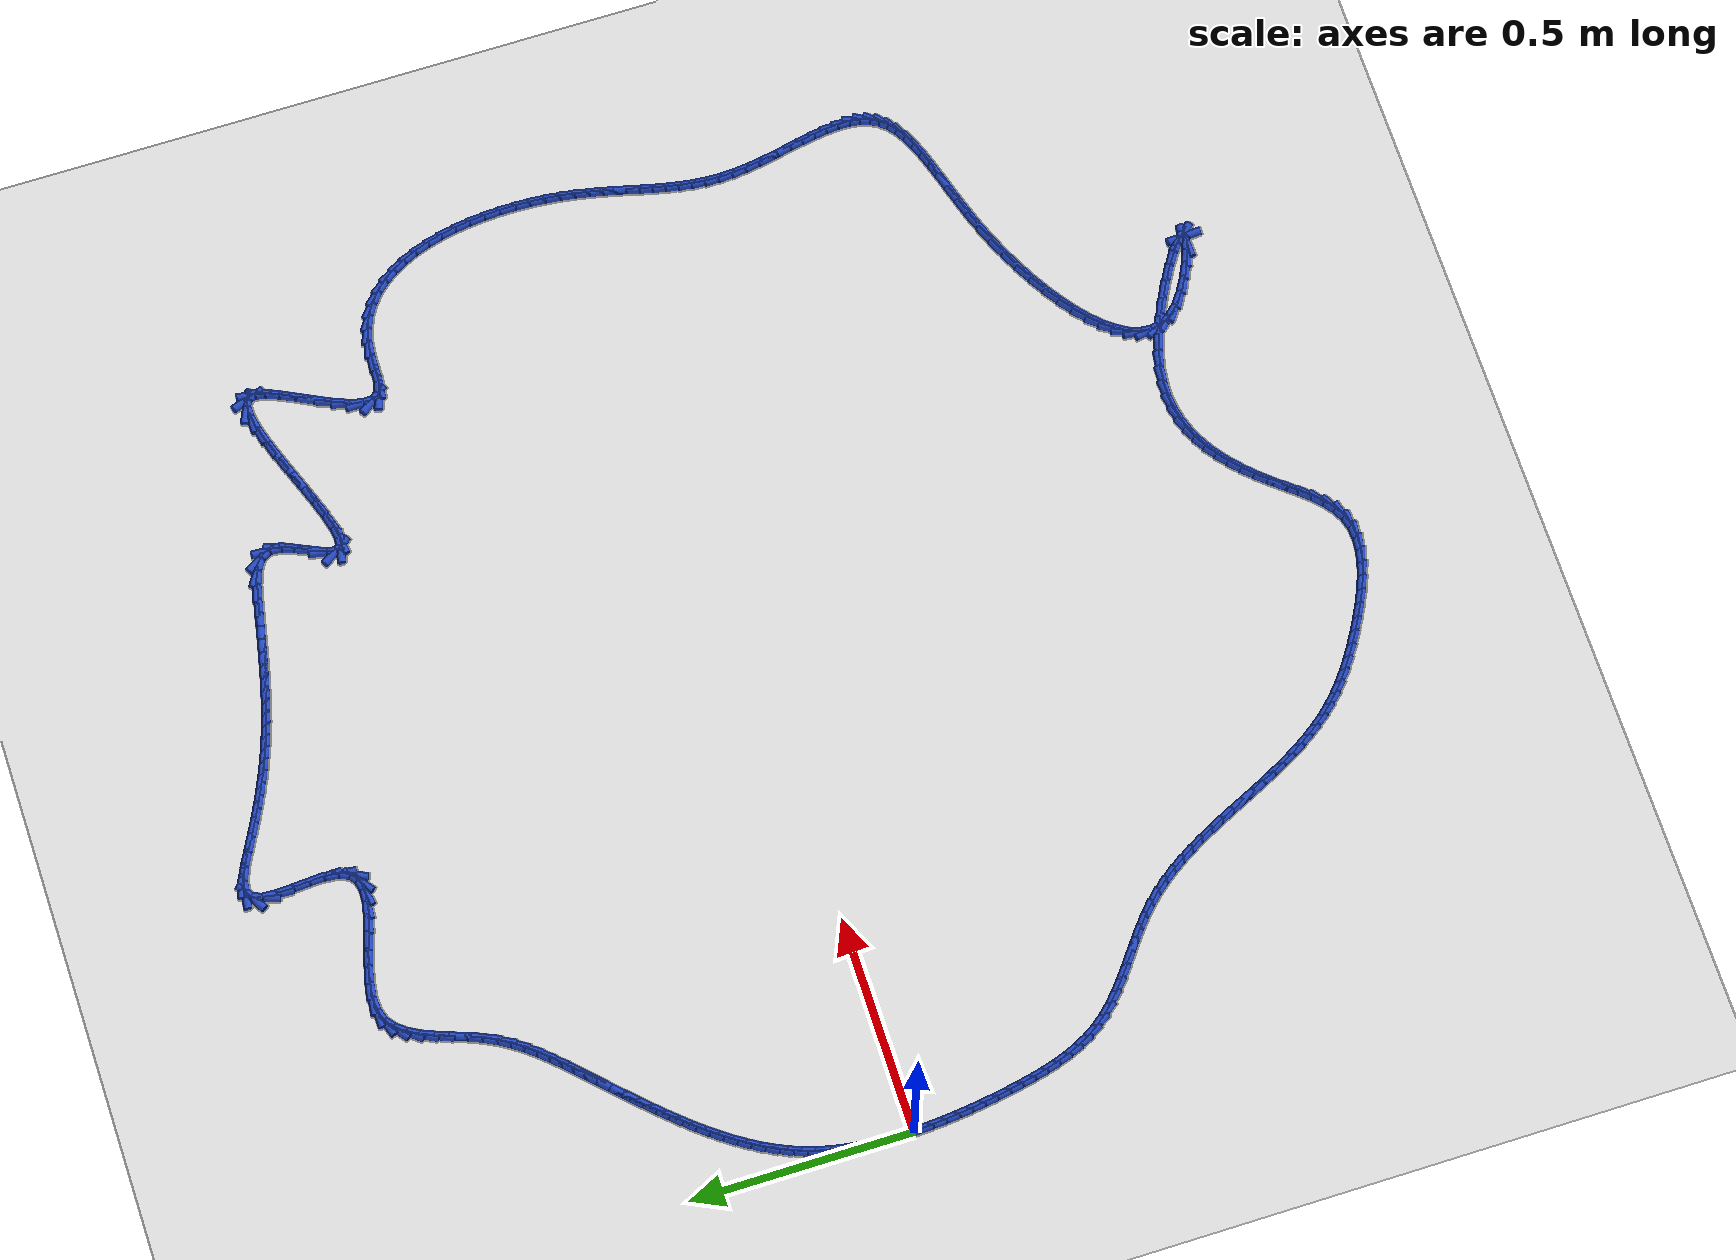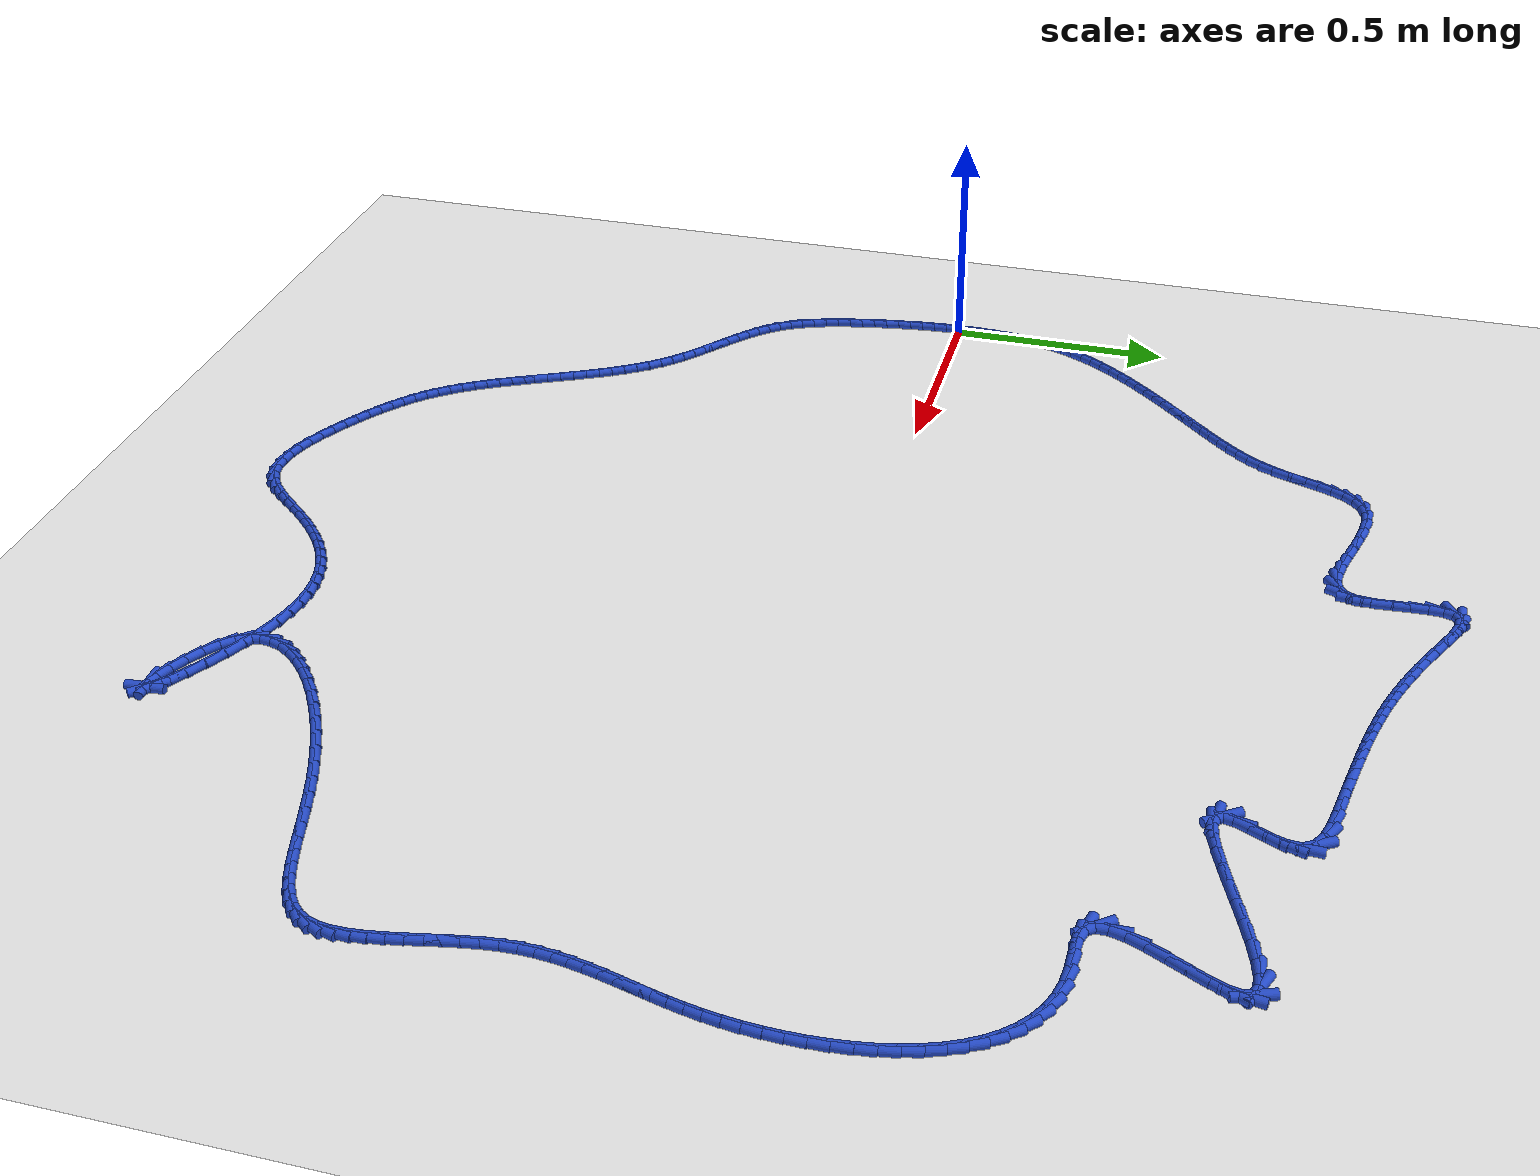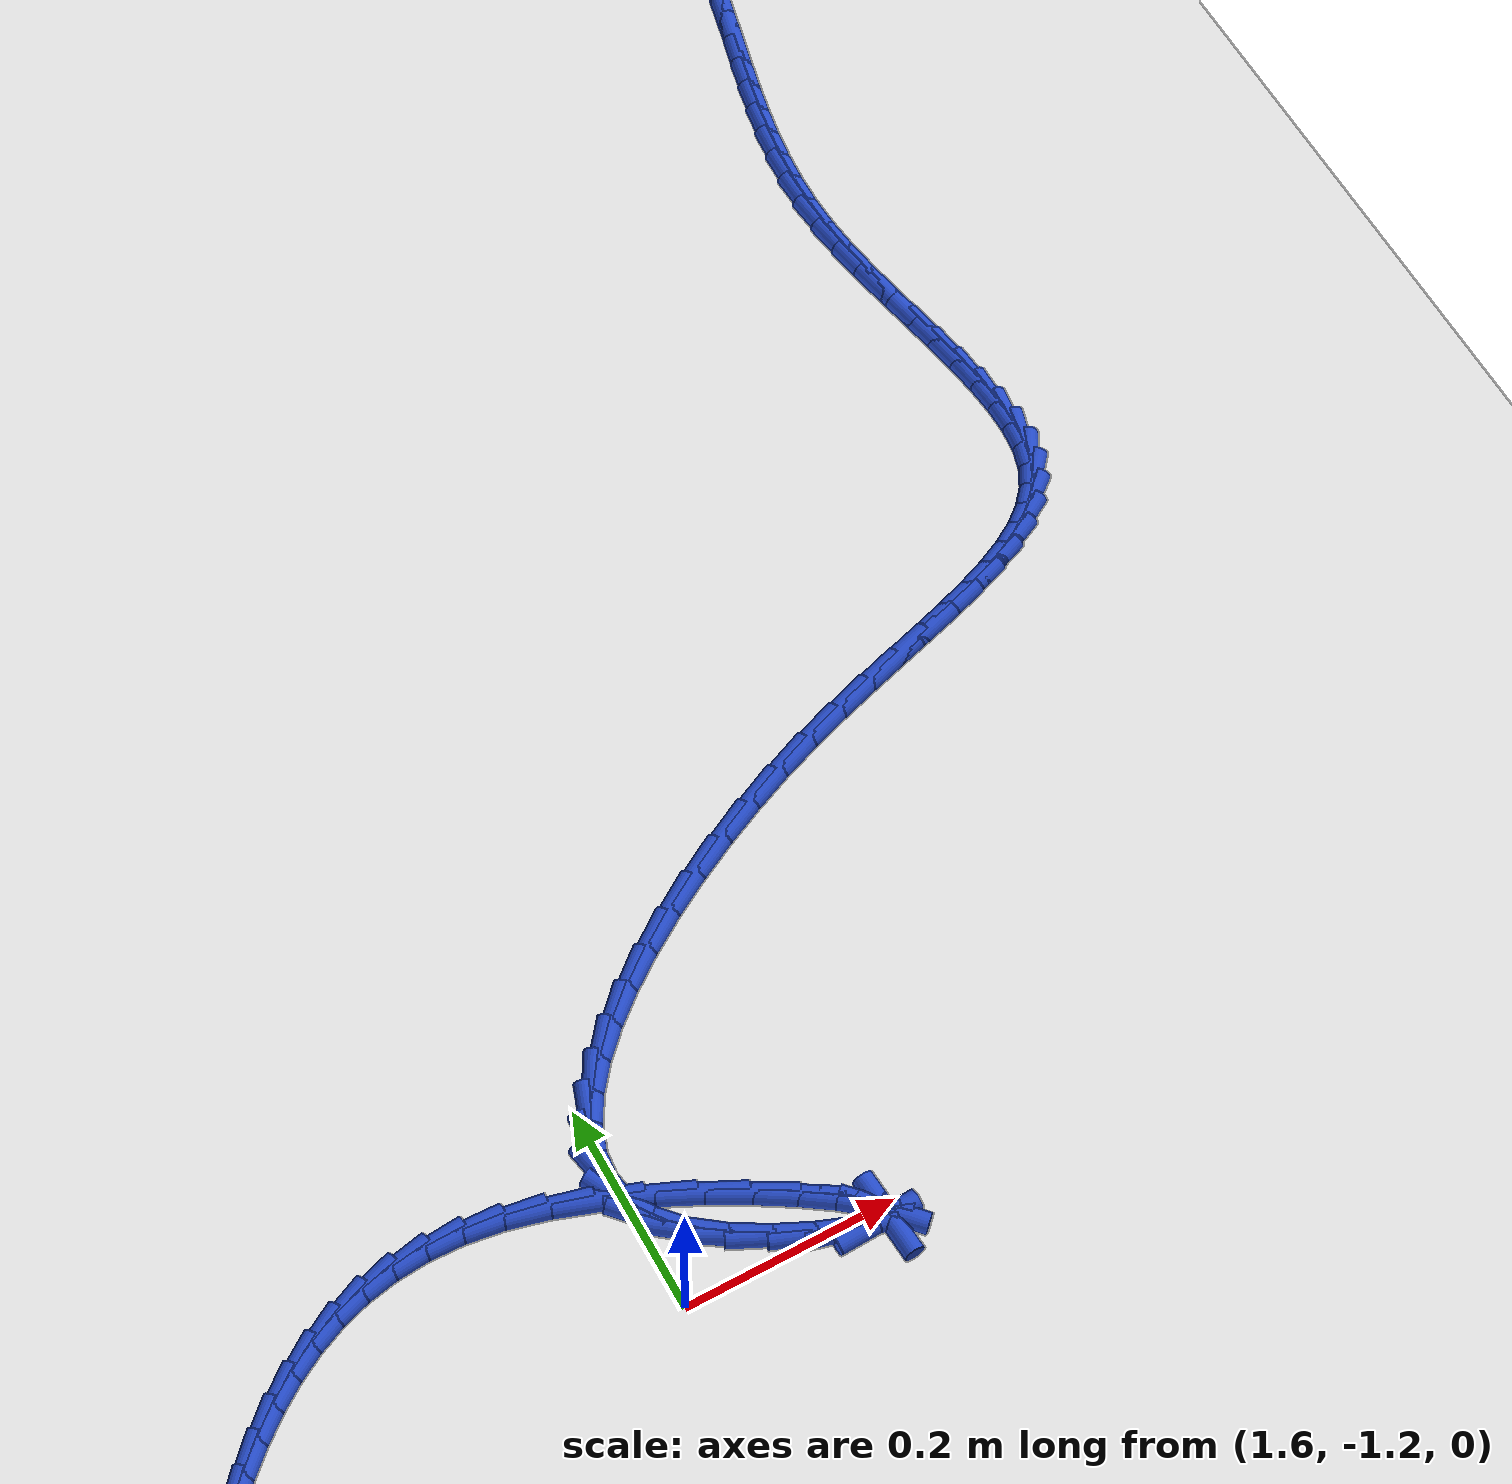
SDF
<sdf version="1.6">
 <world name="default">
  <light name="sun" type="directional">
   <pose>0 0 10 0 -0 0</pose>
   <diffuse>0.8 0.8 0.8 1</diffuse>
   <specular>0.2 0.2 0.2 1</specular>
   <attenuation>
    <range>1000</range>
    <constant>0.9</constant>
    <linear>0.01</linear>
    <quadratic>0.001</quadratic>
   </attenuation>
   <direction>-0.5 0.1 -0.9</direction>
  </light>
  <model name="ground_plane">
   <static>1</static>
   <link name="link">
    <collision name="collision">
     <geometry><plane><normal>0 0 1</normal><size>100 100</size></plane></geometry>
     <surface><friction><ode><mu>100</mu><mu2>50</mu2></ode></friction></surface>
    </collision>
    <visual name="visual">
     <cast_shadows>0</cast_shadows>
     <geometry><plane><normal>0 0 1</normal><size>100 100</size></plane></geometry>
     <material>
      <script><uri>file://media/materials/scripts/gazebo.material</uri><name>Gazebo/WhiteGlow</name></script>
     </material>
    </visual>
   </link>
  </model>
  <gravity>0 0 -9.8</gravity>
  <magnetic_field>6e-06 2.3e-05 -4.2e-05</magnetic_field>
  <atmosphere type="adiabatic"/>
  <physics name="default_physics" default="0" type="ode">
   <max_step_size>0.001</max_step_size>
   <real_time_factor>1</real_time_factor>
   <real_time_update_rate>1000</real_time_update_rate>
  </physics>
  <scene><ambient>0.4 0.4 0.4 1</ambient><background>0.7 0.7 0.7 1</background><shadows>1</shadows></scene>
  <spherical_coordinates>
   <surface_model>EARTH_WGS84</surface_model>
   <latitude_deg>0</latitude_deg>
   <longitude_deg>0</longitude_deg>
   <elevation>0</elevation>
   <heading_deg>0</heading_deg>
  </spherical_coordinates>
  <model name="line">
   <link name="link_0">
    <pose>4.336808689942018e-19 -4.85722573273506e-17 0.01 0 1.57 -1.557330671674084</pose>
    <collision name="collision">
     <geometry><cylinder><radius>0.01</radius><length>0.08</length></cylinder></geometry>
    </collision>
    <visual name="visual">
     <material>
      <script><name>Gazebo/Blue</name><uri>file://media/materials/scripts/gazebo.material</uri></script>
     </material>
     <geometry><cylinder><radius>0.01</radius><length>0.08</length></cylinder></geometry>
    </visual>
   </link>
   <link name="link_1">
    <pose>-0.00040750909841996545 0.030261020655215857 0.01 0 1.57 1.5542438206750813</pose>
    <collision name="collision">
     <geometry><cylinder><radius>0.01</radius><length>0.08</length></cylinder></geometry>
    </collision>
    <visual name="visual">
     <material>
      <script><name>Gazebo/Blue</name><uri>file://media/materials/scripts/gazebo.material</uri></script>
     </material>
     <geometry><cylinder><radius>0.01</radius><length>0.08</length></cylinder></geometry>
    </visual>
   </link>
   <link name="link_2">
    <pose>9.522308559340646e-05 0.06063021464714905 0.01 0 1.57 1.5196190682958277</pose>
    <collision name="collision">
     <geometry><cylinder><radius>0.01</radius><length>0.08</length></cylinder></geometry>
    </collision>
    <visual name="visual">
     <material>
      <script><name>Gazebo/Blue</name><uri>file://media/materials/scripts/gazebo.material</uri></script>
     </material>
     <geometry><cylinder><radius>0.01</radius><length>0.08</length></cylinder></geometry>
    </visual>
   </link>
   <link name="link_3">
    <pose>0.0016496046698707635 0.09097619955869332 0.01 0 1.57 1.480045543788622</pose>
    <collision name="collision">
     <geometry><cylinder><radius>0.01</radius><length>0.08</length></cylinder></geometry>
    </collision>
    <visual name="visual">
     <material>
      <script><name>Gazebo/Blue</name><uri>file://media/materials/scripts/gazebo.material</uri></script>
     </material>
     <geometry><cylinder><radius>0.01</radius><length>0.08</length></cylinder></geometry>
    </visual>
   </link>
   <link name="link_4">
    <pose>0.004397043772242746 0.12116759297274225 0.01 0 1.57 1.43514081480295</pose>
    <collision name="collision">
     <geometry><cylinder><radius>0.01</radius><length>0.08</length></cylinder></geometry>
    </collision>
    <visual name="visual">
     <material>
      <script><name>Gazebo/Blue</name><uri>file://media/materials/scripts/gazebo.material</uri></script>
     </material>
     <geometry><cylinder><radius>0.01</radius><length>0.08</length></cylinder></geometry>
    </visual>
   </link>
   <link name="link_5">
    <pose>0.008478948510540006 0.15107301247218968 0.01 0 1.57 1.384506139608768</pose>
    <collision name="collision">
     <geometry><cylinder><radius>0.01</radius><length>0.08</length></cylinder></geometry>
    </collision>
    <visual name="visual">
     <material>
      <script><name>Gazebo/Blue</name><uri>file://media/materials/scripts/gazebo.material</uri></script>
     </material>
     <geometry><cylinder><radius>0.01</radius><length>0.08</length></cylinder></geometry>
    </visual>
   </link>
   <link name="link_6">
    <pose>0.014036727002593188 0.18056107563992924 0.01 0 1.57 1.3277624946852375</pose>
    <collision name="collision">
     <geometry><cylinder><radius>0.01</radius><length>0.08</length></cylinder></geometry>
    </collision>
    <visual name="visual">
     <material>
      <script><name>Gazebo/Blue</name><uri>file://media/materials/scripts/gazebo.material</uri></script>
     </material>
     <geometry><cylinder><radius>0.01</radius><length>0.08</length></cylinder></geometry>
    </visual>
   </link>
   <link name="link_7">
    <pose>0.02121178736623293 0.20950040005885456 0.01 0 1.57 1.264878874996774</pose>
    <collision name="collision">
     <geometry><cylinder><radius>0.01</radius><length>0.08</length></cylinder></geometry>
    </collision>
    <visual name="visual">
     <material>
      <script><name>Gazebo/Blue</name><uri>file://media/materials/scripts/gazebo.material</uri></script>
     </material>
     <geometry><cylinder><radius>0.01</radius><length>0.08</length></cylinder></geometry>
    </visual>
   </link>
   <link name="link_8">
    <pose>0.030138379030528524 0.2377641429210412 0.01 0 1.57 1.2010551654600476</pose>
    <collision name="collision">
     <geometry><cylinder><radius>0.01</radius><length>0.08</length></cylinder></geometry>
    </collision>
    <visual name="visual">
     <material>
      <script><name>Gazebo/Blue</name><uri>file://media/materials/scripts/gazebo.material</uri></script>
     </material>
     <geometry><cylinder><radius>0.01</radius><length>0.08</length></cylinder></geometry>
    </visual>
   </link>
   <link name="link_9">
    <pose>0.04081483946518975 0.26531164859601863 0.01 0 1.57 1.1413833719987403</pose>
    <collision name="collision">
     <geometry><cylinder><radius>0.01</radius><length>0.08</length></cylinder></geometry>
    </collision>
    <visual name="visual">
     <material>
      <script><name>Gazebo/Blue</name><uri>file://media/materials/scripts/gazebo.material</uri></script>
     </material>
     <geometry><cylinder><radius>0.01</radius><length>0.08</length></cylinder></geometry>
    </visual>
   </link>
   <link name="link_10">
    <pose>0.05311786862572651 0.29217939663752573 0.01 0 1.57 1.0863715544711166</pose>
    <collision name="collision">
     <geometry><cylinder><radius>0.01</radius><length>0.08</length></cylinder></geometry>
    </collision>
    <visual name="visual">
     <material>
      <script><name>Gazebo/Blue</name><uri>file://media/materials/scripts/gazebo.material</uri></script>
     </material>
     <geometry><cylinder><radius>0.01</radius><length>0.08</length></cylinder></geometry>
    </visual>
   </link>
   <link name="link_11">
    <pose>0.06691987369153346 0.31840658881932216 0.01 0 1.57 1.0361963824167704</pose>
    <collision name="collision">
     <geometry><cylinder><radius>0.01</radius><length>0.08</length></cylinder></geometry>
    </collision>
    <visual name="visual">
     <material>
      <script><name>Gazebo/Blue</name><uri>file://media/materials/scripts/gazebo.material</uri></script>
     </material>
     <geometry><cylinder><radius>0.01</radius><length>0.08</length></cylinder></geometry>
    </visual>
   </link>
   <link name="link_12">
    <pose>0.08209326184200522 0.34403242691516717 0.01 0 1.57 0.9909012333198532</pose>
    <collision name="collision">
     <geometry><cylinder><radius>0.01</radius><length>0.08</length></cylinder></geometry>
    </collision>
    <visual name="visual">
     <material>
      <script><name>Gazebo/Blue</name><uri>file://media/materials/scripts/gazebo.material</uri></script>
     </material>
     <geometry><cylinder><radius>0.01</radius><length>0.08</length></cylinder></geometry>
    </visual>
   </link>
   <link name="link_13">
    <pose>0.09851044025653646 0.3690961126988206 0.01 0 1.57 0.9504313867910731</pose>
    <collision name="collision">
     <geometry><cylinder><radius>0.01</radius><length>0.08</length></cylinder></geometry>
    </collision>
    <visual name="visual">
     <material>
      <script><name>Gazebo/Blue</name><uri>file://media/materials/scripts/gazebo.material</uri></script>
     </material>
     <geometry><cylinder><radius>0.01</radius><length>0.08</length></cylinder></geometry>
    </visual>
   </link>
   <link name="link_14">
    <pose>0.11604381611452176 0.39363684794404147 0.01 0 1.57 0.9146671694281283</pose>
    <collision name="collision">
     <geometry><cylinder><radius>0.01</radius><length>0.08</length></cylinder></geometry>
    </collision>
    <visual name="visual">
     <material>
      <script><name>Gazebo/Blue</name><uri>file://media/materials/scripts/gazebo.material</uri></script>
     </material>
     <geometry><cylinder><radius>0.01</radius><length>0.08</length></cylinder></geometry>
    </visual>
   </link>
   <link name="link_15">
    <pose>0.13456579659535586 0.41769383442458974 0.01 0 1.57 0.8834523863434248</pose>
    <collision name="collision">
     <geometry><cylinder><radius>0.01</radius><length>0.08</length></cylinder></geometry>
    </collision>
    <visual name="visual">
     <material>
      <script><name>Gazebo/Blue</name><uri>file://media/materials/scripts/gazebo.material</uri></script>
     </material>
     <geometry><cylinder><radius>0.01</radius><length>0.08</length></cylinder></geometry>
    </visual>
   </link>
   <link name="link_16">
    <pose>0.1539487888784334 0.44130627391422467 0.01 0 1.57 0.856617141175213</pose>
    <collision name="collision">
     <geometry><cylinder><radius>0.01</radius><length>0.08</length></cylinder></geometry>
    </collision>
    <visual name="visual">
     <material>
      <script><name>Gazebo/Blue</name><uri>file://media/materials/scripts/gazebo.material</uri></script>
     </material>
     <geometry><cylinder><radius>0.01</radius><length>0.08</length></cylinder></geometry>
    </visual>
   </link>
   <link name="link_17">
    <pose>0.17406520014314905 0.4645133681867059 0.01 0 1.57 0.8339952775698508</pose>
    <collision name="collision">
     <geometry><cylinder><radius>0.01</radius><length>0.08</length></cylinder></geometry>
    </collision>
    <visual name="visual">
     <material>
      <script><name>Gazebo/Blue</name><uri>file://media/materials/scripts/gazebo.material</uri></script>
     </material>
     <geometry><cylinder><radius>0.01</radius><length>0.08</length></cylinder></geometry>
    </visual>
   </link>
   <link name="link_18">
    <pose>0.19478743756889727 0.4873543190157926 0.01 0 1.57 0.8154372553088627</pose>
    <collision name="collision">
     <geometry><cylinder><radius>0.01</radius><length>0.08</length></cylinder></geometry>
    </collision>
    <visual name="visual">
     <material>
      <script><name>Gazebo/Blue</name><uri>file://media/materials/scripts/gazebo.material</uri></script>
     </material>
     <geometry><cylinder><radius>0.01</radius><length>0.08</length></cylinder></geometry>
    </visual>
   </link>
   <link name="link_19">
    <pose>0.21598790833507295 0.5098683281752447 0.01 0 1.57 0.8008194710903168</pose>
    <collision name="collision">
     <geometry><cylinder><radius>0.01</radius><length>0.08</length></cylinder></geometry>
    </collision>
    <visual name="visual">
     <material>
      <script><name>Gazebo/Blue</name><uri>file://media/materials/scripts/gazebo.material</uri></script>
     </material>
     <geometry><cylinder><radius>0.01</radius><length>0.08</length></cylinder></geometry>
    </visual>
   </link>
   <link name="link_20">
    <pose>0.23753901962107063 0.5320945974388215 0.01 0 1.57 0.7900510066600823</pose>
    <collision name="collision">
     <geometry><cylinder><radius>0.01</radius><length>0.08</length></cylinder></geometry>
    </collision>
    <visual name="visual">
     <material>
      <script><name>Gazebo/Blue</name><uri>file://media/materials/scripts/gazebo.material</uri></script>
     </material>
     <geometry><cylinder><radius>0.01</radius><length>0.08</length></cylinder></geometry>
    </visual>
   </link>
   <link name="link_21">
    <pose>0.259313178606285 0.5540723285802825 0.01 0 1.57 0.7830786512952228</pose>
    <collision name="collision">
     <geometry><cylinder><radius>0.01</radius><length>0.08</length></cylinder></geometry>
    </collision>
    <visual name="visual">
     <material>
      <script><name>Gazebo/Blue</name><uri>file://media/materials/scripts/gazebo.material</uri></script>
     </material>
     <geometry><cylinder><radius>0.01</radius><length>0.08</length></cylinder></geometry>
    </visual>
   </link>
   <link name="link_22">
    <pose>0.28118279247011063 0.5758407233733872 0.01 0 1.57 0.7798908713360476</pose>
    <collision name="collision">
     <geometry><cylinder><radius>0.01</radius><length>0.08</length></cylinder></geometry>
    </collision>
    <visual name="visual">
     <material>
      <script><name>Gazebo/Blue</name><uri>file://media/materials/scripts/gazebo.material</uri></script>
     </material>
     <geometry><cylinder><radius>0.01</radius><length>0.08</length></cylinder></geometry>
    </visual>
   </link>
   <link name="link_23">
    <pose>0.30302026839194224 0.5974389835918952 0.01 0 1.57 0.7805212200813494</pose>
    <collision name="collision">
     <geometry><cylinder><radius>0.01</radius><length>0.08</length></cylinder></geometry>
    </collision>
    <visual name="visual">
     <material>
      <script><name>Gazebo/Blue</name><uri>file://media/materials/scripts/gazebo.material</uri></script>
     </material>
     <geometry><cylinder><radius>0.01</radius><length>0.08</length></cylinder></geometry>
    </visual>
   </link>
   <link name="link_24">
    <pose>0.32469801355117456 0.6189063110095661 0.01 0 1.57 0.7850515053370127</pose>
    <collision name="collision">
     <geometry><cylinder><radius>0.01</radius><length>0.08</length></cylinder></geometry>
    </collision>
    <visual name="visual">
     <material>
      <script><name>Gazebo/Blue</name><uri>file://media/materials/scripts/gazebo.material</uri></script>
     </material>
     <geometry><cylinder><radius>0.01</radius><length>0.08</length></cylinder></geometry>
    </visual>
   </link>
   <link name="link_25">
    <pose>0.3460884351272021 0.6402819074001589 0.01 0 1.57 0.7939475017965634</pose>
    <collision name="collision">
     <geometry><cylinder><radius>0.01</radius><length>0.08</length></cylinder></geometry>
    </collision>
    <visual name="visual">
     <material>
      <script><name>Gazebo/Blue</name><uri>file://media/materials/scripts/gazebo.material</uri></script>
     </material>
     <geometry><cylinder><radius>0.01</radius><length>0.08</length></cylinder></geometry>
    </visual>
   </link>
   <link name="link_26">
    <pose>0.3670614657286973 0.6616166502868205 0.01 0 1.57 0.8125721955080066</pose>
    <collision name="collision">
     <geometry><cylinder><radius>0.01</radius><length>0.08</length></cylinder></geometry>
    </collision>
    <visual name="visual">
     <material>
      <script><name>Gazebo/Blue</name><uri>file://media/materials/scripts/gazebo.material</uri></script>
     </material>
     <geometry><cylinder><radius>0.01</radius><length>0.08</length></cylinder></geometry>
    </visual>
   </link>
   <link name="link_27">
    <pose>0.38744855752923324 0.6831429791551384 0.01 0 1.57 0.845081043685781</pose>
    <collision name="collision">
     <geometry><cylinder><radius>0.01</radius><length>0.08</length></cylinder></geometry>
    </collision>
    <visual name="visual">
     <material>
      <script><name>Gazebo/Blue</name><uri>file://media/materials/scripts/gazebo.material</uri></script>
     </material>
     <geometry><cylinder><radius>0.01</radius><length>0.08</length></cylinder></geometry>
    </visual>
   </link>
   <link name="link_28">
    <pose>0.4070507789272187 0.7052366930403261 0.01 0 1.57 0.8911798800675097</pose>
    <collision name="collision">
     <geometry><cylinder><radius>0.01</radius><length>0.08</length></cylinder></geometry>
    </collision>
    <visual name="visual">
     <material>
      <script><name>Gazebo/Blue</name><uri>file://media/materials/scripts/gazebo.material</uri></script>
     </material>
     <geometry><cylinder><radius>0.01</radius><length>0.08</length></cylinder></geometry>
    </visual>
   </link>
   <link name="link_29">
    <pose>0.4256683714655156 0.7282774923242242 0.01 0 1.57 0.9497921583643891</pose>
    <collision name="collision">
     <geometry><cylinder><radius>0.01</radius><length>0.08</length></cylinder></geometry>
    </collision>
    <visual name="visual">
     <material>
      <script><name>Gazebo/Blue</name><uri>file://media/materials/scripts/gazebo.material</uri></script>
     </material>
     <geometry><cylinder><radius>0.01</radius><length>0.08</length></cylinder></geometry>
    </visual>
   </link>
   <link name="link_30">
    <pose>0.44310157668698585 0.7526450773886726 0.01 0 1.57 1.0190446234355461</pose>
    <collision name="collision">
     <geometry><cylinder><radius>0.01</radius><length>0.08</length></cylinder></geometry>
    </collision>
    <visual name="visual">
     <material>
      <script><name>Gazebo/Blue</name><uri>file://media/materials/scripts/gazebo.material</uri></script>
     </material>
     <geometry><cylinder><radius>0.01</radius><length>0.08</length></cylinder></geometry>
    </visual>
   </link>
   <link name="link_31">
    <pose>0.45915063613449203 0.778719148615513 0.01 0 1.57 1.0962704951491666</pose>
    <collision name="collision">
     <geometry><cylinder><radius>0.01</radius><length>0.08</length></cylinder></geometry>
    </collision>
    <visual name="visual">
     <material>
      <script><name>Gazebo/Blue</name><uri>file://media/materials/scripts/gazebo.material</uri></script>
     </material>
     <geometry><cylinder><radius>0.01</radius><length>0.08</length></cylinder></geometry>
    </visual>
   </link>
   <link name="link_32">
    <pose>0.4736157913508956 0.8068794063865846 0.01 0 1.57 1.172967278083719</pose>
    <collision name="collision">
     <geometry><cylinder><radius>0.01</radius><length>0.08</length></cylinder></geometry>
    </collision>
    <visual name="visual">
     <material>
      <script><name>Gazebo/Blue</name><uri>file://media/materials/scripts/gazebo.material</uri></script>
     </material>
     <geometry><cylinder><radius>0.01</radius><length>0.08</length></cylinder></geometry>
    </visual>
   </link>
   <link name="link_33">
    <pose>0.4864101981601062 0.8373251327337724 0.01 0 1.57 1.2152845462667368</pose>
    <collision name="collision">
     <geometry><cylinder><radius>0.01</radius><length>0.08</length></cylinder></geometry>
    </collision>
    <visual name="visual">
     <material>
      <script><name>Gazebo/Blue</name><uri>file://media/materials/scripts/gazebo.material</uri></script>
     </material>
     <geometry><cylinder><radius>0.01</radius><length>0.08</length></cylinder></geometry>
    </visual>
   </link>
   <link name="link_34">
    <pose>0.49819381989587425 0.8690623347780214 0.01 0 1.57 1.214675562485103</pose>
    <collision name="collision">
     <geometry><cylinder><radius>0.01</radius><length>0.08</length></cylinder></geometry>
    </collision>
    <visual name="visual">
     <material>
      <script><name>Gazebo/Blue</name><uri>file://media/materials/scripts/gazebo.material</uri></script>
     </material>
     <geometry><cylinder><radius>0.01</radius><length>0.08</length></cylinder></geometry>
    </visual>
   </link>
   <link name="link_35">
    <pose>0.5099298609017456 0.9006124906496216 0.01 0 1.57 1.1702819057713336</pose>
    <collision name="collision">
     <geometry><cylinder><radius>0.01</radius><length>0.08</length></cylinder></geometry>
    </collision>
    <visual name="visual">
     <material>
      <script><name>Gazebo/Blue</name><uri>file://media/materials/scripts/gazebo.material</uri></script>
     </material>
     <geometry><cylinder><radius>0.01</radius><length>0.08</length></cylinder></geometry>
    </visual>
   </link>
   <link name="link_36">
    <pose>0.522582397383484 0.9304956853872098 0.01 0 1.57 1.0729018063937743</pose>
    <collision name="collision">
     <geometry><cylinder><radius>0.01</radius><length>0.08</length></cylinder></geometry>
    </collision>
    <visual name="visual">
     <material>
      <script><name>Gazebo/Blue</name><uri>file://media/materials/scripts/gazebo.material</uri></script>
     </material>
     <geometry><cylinder><radius>0.01</radius><length>0.08</length></cylinder></geometry>
    </visual>
   </link>
   <link name="link_37">
    <pose>0.5371155055468513 0.957232004029422 0.01 0 1.57 0.9046597573605681</pose>
    <collision name="collision">
     <geometry><cylinder><radius>0.01</radius><length>0.08</length></cylinder></geometry>
    </collision>
    <visual name="visual">
     <material>
      <script><name>Gazebo/Blue</name><uri>file://media/materials/scripts/gazebo.material</uri></script>
     </material>
     <geometry><cylinder><radius>0.01</radius><length>0.08</length></cylinder></geometry>
    </visual>
   </link>
   <link name="link_38">
    <pose>0.5544932615976108 0.9793415316148942 0.01 0 1.57 0.6469047183386464</pose>
    <collision name="collision">
     <geometry><cylinder><radius>0.01</radius><length>0.08</length></cylinder></geometry>
    </collision>
    <visual name="visual">
     <material>
      <script><name>Gazebo/Blue</name><uri>file://media/materials/scripts/gazebo.material</uri></script>
     </material>
     <geometry><cylinder><radius>0.01</radius><length>0.08</length></cylinder></geometry>
    </visual>
   </link>
   <link name="link_39">
    <pose>0.5756797417415255 0.9953443531822634 0.01 0 1.57 0.3175994807084557</pose>
    <collision name="collision">
     <geometry><cylinder><radius>0.01</radius><length>0.08</length></cylinder></geometry>
    </collision>
    <visual name="visual">
     <material>
      <script><name>Gazebo/Blue</name><uri>file://media/materials/scripts/gazebo.material</uri></script>
     </material>
     <geometry><cylinder><radius>0.01</radius><length>0.08</length></cylinder></geometry>
    </visual>
   </link>
   <link name="link_40">
    <pose>0.6015739367949202 1.0038564839758592 0.01 0 1.57 0.04253857525797999</pose>
    <collision name="collision">
     <geometry><cylinder><radius>0.01</radius><length>0.08</length></cylinder></geometry>
    </collision>
    <visual name="visual">
     <material>
      <script><name>Gazebo/Blue</name><uri>file://media/materials/scripts/gazebo.material</uri></script>
     </material>
     <geometry><cylinder><radius>0.01</radius><length>0.08</length></cylinder></geometry>
    </visual>
   </link>
   <link name="link_41">
    <pose>0.6319516048017316 1.0051494866958663 0.01 0 1.57 -0.1257024147579277</pose>
    <collision name="collision">
     <geometry><cylinder><radius>0.01</radius><length>0.08</length></cylinder></geometry>
    </collision>
    <visual name="visual">
     <material>
      <script><name>Gazebo/Blue</name><uri>file://media/materials/scripts/gazebo.material</uri></script>
     </material>
     <geometry><cylinder><radius>0.01</radius><length>0.08</length></cylinder></geometry>
    </visual>
   </link>
   <link name="link_42">
    <pose>0.6656404514666105 1.0008922707696166 0.01 0 1.57 -0.22238175102146673</pose>
    <collision name="collision">
     <geometry><cylinder><radius>0.01</radius><length>0.08</length></cylinder></geometry>
    </collision>
    <visual name="visual">
     <material>
      <script><name>Gazebo/Blue</name><uri>file://media/materials/scripts/gazebo.material</uri></script>
     </material>
     <geometry><cylinder><radius>0.01</radius><length>0.08</length></cylinder></geometry>
    </visual>
   </link>
   <link name="link_43">
    <pose>0.7014384492495381 0.9927975698421629 0.01 0 1.57 -0.2715432826853941</pose>
    <collision name="collision">
     <geometry><cylinder><radius>0.01</radius><length>0.08</length></cylinder></geometry>
    </collision>
    <visual name="visual">
     <material>
      <script><name>Gazebo/Blue</name><uri>file://media/materials/scripts/gazebo.material</uri></script>
     </material>
     <geometry><cylinder><radius>0.01</radius><length>0.08</length></cylinder></geometry>
    </visual>
   </link>
   <link name="link_44">
    <pose>0.7381435706104956 0.9825781175585571 0.01 0 1.57 -0.2840933482605073</pose>
    <collision name="collision">
     <geometry><cylinder><radius>0.01</radius><length>0.08</length></cylinder></geometry>
    </collision>
    <visual name="visual">
     <material>
      <script><name>Gazebo/Blue</name><uri>file://media/materials/scripts/gazebo.material</uri></script>
     </material>
     <geometry><cylinder><radius>0.01</radius><length>0.08</length></cylinder></geometry>
    </visual>
   </link>
   <link name="link_45">
    <pose>0.7745537880094636 0.9719466475638514 0.01 0 1.57 -0.2611516877198603</pose>
    <collision name="collision">
     <geometry><cylinder><radius>0.01</radius><length>0.08</length></cylinder></geometry>
    </collision>
    <visual name="visual">
     <material>
      <script><name>Gazebo/Blue</name><uri>file://media/materials/scripts/gazebo.material</uri></script>
     </material>
     <geometry><cylinder><radius>0.01</radius><length>0.08</length></cylinder></geometry>
    </visual>
   </link>
   <link name="link_46">
    <pose>0.8094670739064234 0.9626158935030983 0.01 0 1.57 -0.19364500436426565</pose>
    <collision name="collision">
     <geometry><cylinder><radius>0.01</radius><length>0.08</length></cylinder></geometry>
    </collision>
    <visual name="visual">
     <material>
      <script><name>Gazebo/Blue</name><uri>file://media/materials/scripts/gazebo.material</uri></script>
     </material>
     <geometry><cylinder><radius>0.01</radius><length>0.08</length></cylinder></geometry>
    </visual>
   </link>
   <link name="link_47">
    <pose>0.8416814007613558 0.9562985890213502 0.01 0 1.57 -0.05613782908101078</pose>
    <collision name="collision">
     <geometry><cylinder><radius>0.01</radius><length>0.08</length></cylinder></geometry>
    </collision>
    <visual name="visual">
     <material>
      <script><name>Gazebo/Blue</name><uri>file://media/materials/scripts/gazebo.material</uri></script>
     </material>
     <geometry><cylinder><radius>0.01</radius><length>0.08</length></cylinder></geometry>
    </visual>
   </link>
   <link name="link_48">
    <pose>0.869994741034242 0.9547074677636591 0.01 0 1.57 0.20590368198363146</pose>
    <collision name="collision">
     <geometry><cylinder><radius>0.01</radius><length>0.08</length></cylinder></geometry>
    </collision>
    <visual name="visual">
     <material>
      <script><name>Gazebo/Blue</name><uri>file://media/materials/scripts/gazebo.material</uri></script>
     </material>
     <geometry><cylinder><radius>0.01</radius><length>0.08</length></cylinder></geometry>
    </visual>
   </link>
   <link name="link_49">
    <pose>0.8932050671850628 0.9595552633750776 0.01 0 1.57 0.6555239522027402</pose>
    <collision name="collision">
     <geometry><cylinder><radius>0.01</radius><length>0.08</length></cylinder></geometry>
    </collision>
    <visual name="visual">
     <material>
      <script><name>Gazebo/Blue</name><uri>file://media/materials/scripts/gazebo.material</uri></script>
     </material>
     <geometry><cylinder><radius>0.01</radius><length>0.08</length></cylinder></geometry>
    </visual>
   </link>
   <link name="link_50">
    <pose>0.9101103516737993 0.9725547095006578 0.01 0 1.57 1.172671231263273</pose>
    <collision name="collision">
     <geometry><cylinder><radius>0.01</radius><length>0.08</length></cylinder></geometry>
    </collision>
    <visual name="visual">
     <material>
      <script><name>Gazebo/Blue</name><uri>file://media/materials/scripts/gazebo.material</uri></script>
     </material>
     <geometry><cylinder><radius>0.01</radius><length>0.08</length></cylinder></geometry>
    </visual>
   </link>
   <link name="link_51">
    <pose>0.9196453515854078 0.9952255176161227 0.01 0 1.57 1.47172185277886</pose>
    <collision name="collision">
     <geometry><cylinder><radius>0.01</radius><length>0.08</length></cylinder></geometry>
    </collision>
    <visual name="visual">
     <material>
      <script><name>Gazebo/Blue</name><uri>file://media/materials/scripts/gazebo.material</uri></script>
     </material>
     <geometry><cylinder><radius>0.01</radius><length>0.08</length></cylinder></geometry>
    </visual>
   </link>
   <link name="link_52">
    <pose>0.9227324246954024 1.0262826176135769 0.01 0 1.57 -1.5447732184338276</pose>
    <collision name="collision">
     <geometry><cylinder><radius>0.01</radius><length>0.08</length></cylinder></geometry>
    </collision>
    <visual name="visual">
     <material>
      <script><name>Gazebo/Blue</name><uri>file://media/materials/scripts/gazebo.material</uri></script>
     </material>
     <geometry><cylinder><radius>0.01</radius><length>0.08</length></cylinder></geometry>
    </visual>
   </link>
   <link name="link_53">
    <pose>0.9217943122090171 1.0623236892593673 0.01 0 1.57 -1.5042565350602122</pose>
    <collision name="collision">
     <geometry><cylinder><radius>0.01</radius><length>0.08</length></cylinder></geometry>
    </collision>
    <visual name="visual">
     <material>
      <script><name>Gazebo/Blue</name><uri>file://media/materials/scripts/gazebo.material</uri></script>
     </material>
     <geometry><cylinder><radius>0.01</radius><length>0.08</length></cylinder></geometry>
    </visual>
   </link>
   <link name="link_54">
    <pose>0.9192906745757944 1.099894314120735 0.01 0 1.57 -1.5256742734886328</pose>
    <collision name="collision">
     <geometry><cylinder><radius>0.01</radius><length>0.08</length></cylinder></geometry>
    </collision>
    <visual name="visual">
     <material>
      <script><name>Gazebo/Blue</name><uri>file://media/materials/scripts/gazebo.material</uri></script>
     </material>
     <geometry><cylinder><radius>0.01</radius><length>0.08</length></cylinder></geometry>
    </visual>
   </link>
   <link name="link_55">
    <pose>0.917681172245277 1.1355400737649213 0.01 0 1.57 1.5132288015301205</pose>
    <collision name="collision">
     <geometry><cylinder><radius>0.01</radius><length>0.08</length></cylinder></geometry>
    </collision>
    <visual name="visual">
     <material>
      <script><name>Gazebo/Blue</name><uri>file://media/materials/scripts/gazebo.material</uri></script>
     </material>
     <geometry><cylinder><radius>0.01</radius><length>0.08</length></cylinder></geometry>
    </visual>
   </link>
   <link name="link_56">
    <pose>0.9194254656670074 1.1658065497591668 0.01 0 1.57 1.2317841586224976</pose>
    <collision name="collision">
     <geometry><cylinder><radius>0.01</radius><length>0.08</length></cylinder></geometry>
    </collision>
    <visual name="visual">
     <material>
      <script><name>Gazebo/Blue</name><uri>file://media/materials/scripts/gazebo.material</uri></script>
     </material>
     <geometry><cylinder><radius>0.01</radius><length>0.08</length></cylinder></geometry>
    </visual>
   </link>
   <link name="link_57">
    <pose>0.9269832152905287 1.1872393236707137 0.01 0 1.57 0.5317993670149042</pose>
    <collision name="collision">
     <geometry><cylinder><radius>0.01</radius><length>0.08</length></cylinder></geometry>
    </collision>
    <visual name="visual">
     <material>
      <script><name>Gazebo/Blue</name><uri>file://media/materials/scripts/gazebo.material</uri></script>
     </material>
     <geometry><cylinder><radius>0.01</radius><length>0.08</length></cylinder></geometry>
    </visual>
   </link>
   <link name="link_58">
    <pose>0.9427290959804688 1.1965032024244868 0.01 0 1.57 -0.12266862102347689</pose>
    <collision name="collision">
     <geometry><cylinder><radius>0.01</radius><length>0.08</length></cylinder></geometry>
    </collision>
    <visual name="visual">
     <material>
      <script><name>Gazebo/Blue</name><uri>file://media/materials/scripts/gazebo.material</uri></script>
     </material>
     <geometry><cylinder><radius>0.01</radius><length>0.08</length></cylinder></geometry>
    </visual>
   </link>
   <link name="link_59">
    <pose>0.9666959022687049 1.1935483915292808 0.01 0 1.57 -0.37315613800252745</pose>
    <collision name="collision">
     <geometry><cylinder><radius>0.01</radius><length>0.08</length></cylinder></geometry>
    </collision>
    <visual name="visual">
     <material>
      <script><name>Gazebo/Blue</name><uri>file://media/materials/scripts/gazebo.material</uri></script>
     </material>
     <geometry><cylinder><radius>0.01</radius><length>0.08</length></cylinder></geometry>
    </visual>
   </link>
   <link name="link_60">
    <pose>0.9963368069775649 1.1819440198833315 0.01 0 1.57 -0.4680728456625661</pose>
    <collision name="collision">
     <geometry><cylinder><radius>0.01</radius><length>0.08</length></cylinder></geometry>
    </collision>
    <visual name="visual">
     <material>
      <script><name>Gazebo/Blue</name><uri>file://media/materials/scripts/gazebo.material</uri></script>
     </material>
     <geometry><cylinder><radius>0.01</radius><length>0.08</length></cylinder></geometry>
    </visual>
   </link>
   <link name="link_61">
    <pose>1.0289723096795942 1.1654453422517108 0.01 0 1.57 -0.4916380510884422</pose>
    <collision name="collision">
     <geometry><cylinder><radius>0.01</radius><length>0.08</length></cylinder></geometry>
    </collision>
    <visual name="visual">
     <material>
      <script><name>Gazebo/Blue</name><uri>file://media/materials/scripts/gazebo.material</uri></script>
     </material>
     <geometry><cylinder><radius>0.01</radius><length>0.08</length></cylinder></geometry>
    </visual>
   </link>
   <link name="link_62">
    <pose>1.0619317070836891 1.1477957803943486 0.01 0 1.57 -0.4772264739205649</pose>
    <collision name="collision">
     <geometry><cylinder><radius>0.01</radius><length>0.08</length></cylinder></geometry>
    </collision>
    <visual name="visual">
     <material>
      <script><name>Gazebo/Blue</name><uri>file://media/materials/scripts/gazebo.material</uri></script>
     </material>
     <geometry><cylinder><radius>0.01</radius><length>0.08</length></cylinder></geometry>
    </visual>
   </link>
   <link name="link_63">
    <pose>1.0934772106222705 1.1314838949123416 0.01 0 1.57 -0.45735072257823034</pose>
    <collision name="collision">
     <geometry><cylinder><radius>0.01</radius><length>0.08</length></cylinder></geometry>
    </collision>
    <visual name="visual">
     <material>
      <script><name>Gazebo/Blue</name><uri>file://media/materials/scripts/gazebo.material</uri></script>
     </material>
     <geometry><cylinder><radius>0.01</radius><length>0.08</length></cylinder></geometry>
    </visual>
   </link>
   <link name="link_64">
    <pose>1.123616128590934 1.1166509211724487 0.01 0 1.57 -0.43575265361047505</pose>
    <collision name="collision">
     <geometry><cylinder><radius>0.01</radius><length>0.08</length></cylinder></geometry>
    </collision>
    <visual name="visual">
     <material>
      <script><name>Gazebo/Blue</name><uri>file://media/materials/scripts/gazebo.material</uri></script>
     </material>
     <geometry><cylinder><radius>0.01</radius><length>0.08</length></cylinder></geometry>
    </visual>
   </link>
   <link name="link_65">
    <pose>1.1525472561301062 1.103180526086409 0.01 0 1.57 -0.412657409197168</pose>
    <collision name="collision">
     <geometry><cylinder><radius>0.01</radius><length>0.08</length></cylinder></geometry>
    </collision>
    <visual name="visual">
     <material>
      <script><name>Gazebo/Blue</name><uri>file://media/materials/scripts/gazebo.material</uri></script>
     </material>
     <geometry><cylinder><radius>0.01</radius><length>0.08</length></cylinder></geometry>
    </visual>
   </link>
   <link name="link_66">
    <pose>1.1804693883802142 1.090956376565958 0.01 0 1.57 -0.38841325361618595</pose>
    <collision name="collision">
     <geometry><cylinder><radius>0.01</radius><length>0.08</length></cylinder></geometry>
    </collision>
    <visual name="visual">
     <material>
      <script><name>Gazebo/Blue</name><uri>file://media/materials/scripts/gazebo.material</uri></script>
     </material>
     <geometry><cylinder><radius>0.01</radius><length>0.08</length></cylinder></geometry>
    </visual>
   </link>
   <link name="link_67">
    <pose>1.2075813204816834 1.0798621395228352 0.01 0 1.57 -0.36349178252804787</pose>
    <collision name="collision">
     <geometry><cylinder><radius>0.01</radius><length>0.08</length></cylinder></geometry>
    </collision>
    <visual name="visual">
     <material>
      <script><name>Gazebo/Blue</name><uri>file://media/materials/scripts/gazebo.material</uri></script>
     </material>
     <geometry><cylinder><radius>0.01</radius><length>0.08</length></cylinder></geometry>
    </visual>
   </link>
   <link name="link_68">
    <pose>1.2340818475749418 1.0697814818687765 0.01 0 1.57 -0.3384712861107182</pose>
    <collision name="collision">
     <geometry><cylinder><radius>0.01</radius><length>0.08</length></cylinder></geometry>
    </collision>
    <visual name="visual">
     <material>
      <script><name>Gazebo/Blue</name><uri>file://media/materials/scripts/gazebo.material</uri></script>
     </material>
     <geometry><cylinder><radius>0.01</radius><length>0.08</length></cylinder></geometry>
    </visual>
   </link>
   <link name="link_69">
    <pose>1.2601697648004149 1.0605980705155205 0.01 0 1.57 -0.3140016879058001</pose>
    <collision name="collision">
     <geometry><cylinder><radius>0.01</radius><length>0.08</length></cylinder></geometry>
    </collision>
    <visual name="visual">
     <material>
      <script><name>Gazebo/Blue</name><uri>file://media/materials/scripts/gazebo.material</uri></script>
     </material>
     <geometry><cylinder><radius>0.01</radius><length>0.08</length></cylinder></geometry>
    </visual>
   </link>
   <link name="link_70">
    <pose>1.2860438672985293 1.0521955723748042 0.01 0 1.57 -0.29075393672331684</pose>
    <collision name="collision">
     <geometry><cylinder><radius>0.01</radius><length>0.08</length></cylinder></geometry>
    </collision>
    <visual name="visual">
     <material>
      <script><name>Gazebo/Blue</name><uri>file://media/materials/scripts/gazebo.material</uri></script>
     </material>
     <geometry><cylinder><radius>0.01</radius><length>0.08</length></cylinder></geometry>
    </visual>
   </link>
   <link name="link_71">
    <pose>1.3119029502097113 1.0444576543583655 0.01 0 1.57 -0.26936138847672325</pose>
    <collision name="collision">
     <geometry><cylinder><radius>0.01</radius><length>0.08</length></cylinder></geometry>
    </collision>
    <visual name="visual">
     <material>
      <script><name>Gazebo/Blue</name><uri>file://media/materials/scripts/gazebo.material</uri></script>
     </material>
     <geometry><cylinder><radius>0.01</radius><length>0.08</length></cylinder></geometry>
    </visual>
   </link>
   <link name="link_72">
    <pose>1.3379458086743883 1.037267983377942 0.01 0 1.57 -0.25036365292439866</pose>
    <collision name="collision">
     <geometry><cylinder><radius>0.01</radius><length>0.08</length></cylinder></geometry>
    </collision>
    <visual name="visual">
     <material>
      <script><name>Gazebo/Blue</name><uri>file://media/materials/scripts/gazebo.material</uri></script>
     </material>
     <geometry><cylinder><radius>0.01</radius><length>0.08</length></cylinder></geometry>
    </visual>
   </link>
   <link name="link_73">
    <pose>1.3643712378329862 1.0305102263452706 0.01 0 1.57 -0.23416317445444537</pose>
    <collision name="collision">
     <geometry><cylinder><radius>0.01</radius><length>0.08</length></cylinder></geometry>
    </collision>
    <visual name="visual">
     <material>
      <script><name>Gazebo/Blue</name><uri>file://media/materials/scripts/gazebo.material</uri></script>
     </material>
     <geometry><cylinder><radius>0.01</radius><length>0.08</length></cylinder></geometry>
    </visual>
   </link>
   <link name="link_74">
    <pose>1.3913780328259313 1.0240680501720896 0.01 0 1.57 -0.22100145210969668</pose>
    <collision name="collision">
     <geometry><cylinder><radius>0.01</radius><length>0.08</length></cylinder></geometry>
    </collision>
    <visual name="visual">
     <material>
      <script><name>Gazebo/Blue</name><uri>file://media/materials/scripts/gazebo.material</uri></script>
     </material>
     <geometry><cylinder><radius>0.01</radius><length>0.08</length></cylinder></geometry>
    </visual>
   </link>
   <link name="link_75">
    <pose>1.4191649887936504 1.017825121770136 0.01 0 1.57 -0.21095671451756762</pose>
    <collision name="collision">
     <geometry><cylinder><radius>0.01</radius><length>0.08</length></cylinder></geometry>
    </collision>
    <visual name="visual">
     <material>
      <script><name>Gazebo/Blue</name><uri>file://media/materials/scripts/gazebo.material</uri></script>
     </material>
     <geometry><cylinder><radius>0.01</radius><length>0.08</length></cylinder></geometry>
    </visual>
   </link>
   <link name="link_76">
    <pose>1.4479309008765697 1.0116651080511476 0.01 0 1.57 -0.20396005924692726</pose>
    <collision name="collision">
     <geometry><cylinder><radius>0.01</radius><length>0.08</length></cylinder></geometry>
    </collision>
    <visual name="visual">
     <material>
      <script><name>Gazebo/Blue</name><uri>file://media/materials/scripts/gazebo.material</uri></script>
     </material>
     <geometry><cylinder><radius>0.01</radius><length>0.08</length></cylinder></geometry>
    </visual>
   </link>
   <link name="link_77">
    <pose>1.477874564215116 1.005471675926862 0.01 0 1.57 -0.19982404456002997</pose>
    <collision name="collision">
     <geometry><cylinder><radius>0.01</radius><length>0.08</length></cylinder></geometry>
    </collision>
    <visual name="visual">
     <material>
      <script><name>Gazebo/Blue</name><uri>file://media/materials/scripts/gazebo.material</uri></script>
     </material>
     <geometry><cylinder><radius>0.01</radius><length>0.08</length></cylinder></geometry>
    </visual>
   </link>
   <link name="link_78">
    <pose>1.5091947739497167 0.9991284923090165 0.01 0 1.57 -0.1982769223530124</pose>
    <collision name="collision">
     <geometry><cylinder><radius>0.01</radius><length>0.08</length></cylinder></geometry>
    </collision>
    <visual name="visual">
     <material>
      <script><name>Gazebo/Blue</name><uri>file://media/materials/scripts/gazebo.material</uri></script>
     </material>
     <geometry><cylinder><radius>0.01</radius><length>0.08</length></cylinder></geometry>
    </visual>
   </link>
   <link name="link_79">
    <pose>1.5420903252207965 0.9925192241093486 0.01 0 1.57 -0.19904461592035877</pose>
    <collision name="collision">
     <geometry><cylinder><radius>0.01</radius><length>0.08</length></cylinder></geometry>
    </collision>
    <visual name="visual">
     <material>
      <script><name>Gazebo/Blue</name><uri>file://media/materials/scripts/gazebo.material</uri></script>
     </material>
     <geometry><cylinder><radius>0.01</radius><length>0.08</length></cylinder></geometry>
    </visual>
   </link>
   <link name="link_80">
    <pose>1.5767569604038825 0.9855264234895668 0.01 0 1.57 -0.2200409473014814</pose>
    <collision name="collision">
     <geometry><cylinder><radius>0.01</radius><length>0.08</length></cylinder></geometry>
    </collision>
    <visual name="visual">
     <material>
      <script><name>Gazebo/Blue</name><uri>file://media/materials/scripts/gazebo.material</uri></script>
     </material>
     <geometry><cylinder><radius>0.01</radius><length>0.08</length></cylinder></geometry>
    </visual>
   </link>
   <link name="link_81">
    <pose>1.6122020385916365 0.9775986916380697 0.01 0 1.57 -0.31491738829142585</pose>
    <collision name="collision">
     <geometry><cylinder><radius>0.01</radius><length>0.08</length></cylinder></geometry>
    </collision>
    <visual name="visual">
     <material>
      <script><name>Gazebo/Blue</name><uri>file://media/materials/scripts/gazebo.material</uri></script>
     </material>
     <geometry><cylinder><radius>0.01</radius><length>0.08</length></cylinder></geometry>
    </visual>
   </link>
   <link name="link_82">
    <pose>1.644447501083149 0.9670944722360495 0.01 0 1.57 -0.5442021628274567</pose>
    <collision name="collision">
     <geometry><cylinder><radius>0.01</radius><length>0.08</length></cylinder></geometry>
    </collision>
    <visual name="visual">
     <material>
      <script><name>Gazebo/Blue</name><uri>file://media/materials/scripts/gazebo.material</uri></script>
     </material>
     <geometry><cylinder><radius>0.01</radius><length>0.08</length></cylinder></geometry>
    </visual>
   </link>
   <link name="link_83">
    <pose>1.6690539318658928 0.952203739366291 0.01 0 1.57 -1.034669283786752</pose>
    <collision name="collision">
     <geometry><cylinder><radius>0.01</radius><length>0.08</length></cylinder></geometry>
    </collision>
    <visual name="visual">
     <material>
      <script><name>Gazebo/Blue</name><uri>file://media/materials/scripts/gazebo.material</uri></script>
     </material>
     <geometry><cylinder><radius>0.01</radius><length>0.08</length></cylinder></geometry>
    </visual>
   </link>
   <link name="link_84">
    <pose>1.6815831264479086 0.931117110350725 0.01 0 1.57 1.5085522697786993</pose>
    <collision name="collision">
     <geometry><cylinder><radius>0.01</radius><length>0.08</length></cylinder></geometry>
    </collision>
    <visual name="visual">
     <material>
      <script><name>Gazebo/Blue</name><uri>file://media/materials/scripts/gazebo.material</uri></script>
     </material>
     <geometry><cylinder><radius>0.01</radius><length>0.08</length></cylinder></geometry>
    </visual>
   </link>
   <link name="link_85">
    <pose>1.6798443555793718 0.9032184666600894 0.01 0 1.57 1.2282274467618073</pose>
    <collision name="collision">
     <geometry><cylinder><radius>0.01</radius><length>0.08</length></cylinder></geometry>
    </collision>
    <visual name="visual">
     <material>
      <script><name>Gazebo/Blue</name><uri>file://media/materials/scripts/gazebo.material</uri></script>
     </material>
     <geometry><cylinder><radius>0.01</radius><length>0.08</length></cylinder></geometry>
    </visual>
   </link>
   <link name="link_86">
    <pose>1.6685535266009224 0.8715586675710336 0.01 0 1.57 1.1334893583099654</pose>
    <collision name="collision">
     <geometry><cylinder><radius>0.01</radius><length>0.08</length></cylinder></geometry>
    </collision>
    <visual name="visual">
     <material>
      <script><name>Gazebo/Blue</name><uri>file://media/materials/scripts/gazebo.material</uri></script>
     </material>
     <geometry><cylinder><radius>0.01</radius><length>0.08</length></cylinder></geometry>
    </visual>
   </link>
   <link name="link_87">
    <pose>1.6537488953925668 0.8398906540003813 0.01 0 1.57 1.1564715526220575</pose>
    <collision name="collision">
     <geometry><cylinder><radius>0.01</radius><length>0.08</length></cylinder></geometry>
    </collision>
    <visual name="visual">
     <material>
      <script><name>Gazebo/Blue</name><uri>file://media/materials/scripts/gazebo.material</uri></script>
     </material>
     <geometry><cylinder><radius>0.01</radius><length>0.08</length></cylinder></geometry>
    </visual>
   </link>
   <link name="link_88">
    <pose>1.6414687178343104 0.811967366864958 0.01 0 1.57 1.38871821715873</pose>
    <collision name="collision">
     <geometry><cylinder><radius>0.01</radius><length>0.08</length></cylinder></geometry>
    </collision>
    <visual name="visual">
     <material>
      <script><name>Gazebo/Blue</name><uri>file://media/materials/scripts/gazebo.material</uri></script>
     </material>
     <geometry><cylinder><radius>0.01</radius><length>0.08</length></cylinder></geometry>
    </visual>
   </link>
   <link name="link_89">
    <pose>1.6377019909258206 0.7915090633810091 0.01 0 1.57 -0.9598681090177598</pose>
    <collision name="collision">
     <geometry><cylinder><radius>0.01</radius><length>0.08</length></cylinder></geometry>
    </collision>
    <visual name="visual">
     <material>
      <script><name>Gazebo/Blue</name><uri>file://media/materials/scripts/gazebo.material</uri></script>
     </material>
     <geometry><cylinder><radius>0.01</radius><length>0.08</length></cylinder></geometry>
    </visual>
   </link>
   <link name="link_90">
    <pose>1.6455416175694253 0.7803144168458146 0.01 0 1.57 -0.1691462319148357</pose>
    <collision name="collision">
     <geometry><cylinder><radius>0.01</radius><length>0.08</length></cylinder></geometry>
    </collision>
    <visual name="visual">
     <material>
      <script><name>Gazebo/Blue</name><uri>file://media/materials/scripts/gazebo.material</uri></script>
     </material>
     <geometry><cylinder><radius>0.01</radius><length>0.08</length></cylinder></geometry>
    </visual>
   </link>
   <link name="link_91">
    <pose>1.6636254025529034 0.7772261037531665 0.01 0 1.57 0.13492208402925984</pose>
    <collision name="collision">
     <geometry><cylinder><radius>0.01</radius><length>0.08</length></cylinder></geometry>
    </collision>
    <visual name="visual">
     <material>
      <script><name>Gazebo/Blue</name><uri>file://media/materials/scripts/gazebo.material</uri></script>
     </material>
     <geometry><cylinder><radius>0.01</radius><length>0.08</length></cylinder></geometry>
    </visual>
   </link>
   <link name="link_92">
    <pose>1.6902118453217245 0.7808351281643805 0.01 0 1.57 0.26073320397918986</pose>
    <collision name="collision">
     <geometry><cylinder><radius>0.01</radius><length>0.08</length></cylinder></geometry>
    </collision>
    <visual name="visual">
     <material>
      <script><name>Gazebo/Blue</name><uri>file://media/materials/scripts/gazebo.material</uri></script>
     </material>
     <geometry><cylinder><radius>0.01</radius><length>0.08</length></cylinder></geometry>
    </visual>
   </link>
   <link name="link_93">
    <pose>1.7235594453213592 0.7897324941407727 0.01 0 1.57 0.3214602642262891</pose>
    <collision name="collision">
     <geometry><cylinder><radius>0.01</radius><length>0.08</length></cylinder></geometry>
    </collision>
    <visual name="visual">
     <material>
      <script><name>Gazebo/Blue</name><uri>file://media/materials/scripts/gazebo.material</uri></script>
     </material>
     <geometry><cylinder><radius>0.01</radius><length>0.08</length></cylinder></geometry>
    </visual>
   </link>
   <link name="link_94">
    <pose>1.7619267019972795 0.8025092057436596 0.01 0 1.57 0.35095949890989875</pose>
    <collision name="collision">
     <geometry><cylinder><radius>0.01</radius><length>0.08</length></cylinder></geometry>
    </collision>
    <visual name="visual">
     <material>
      <script><name>Gazebo/Blue</name><uri>file://media/materials/scripts/gazebo.material</uri></script>
     </material>
     <geometry><cylinder><radius>0.01</radius><length>0.08</length></cylinder></geometry>
    </visual>
   </link>
   <link name="link_95">
    <pose>1.8035721147949546 0.8177562670343568 0.01 0 1.57 0.36110625869679286</pose>
    <collision name="collision">
     <geometry><cylinder><radius>0.01</radius><length>0.08</length></cylinder></geometry>
    </collision>
    <visual name="visual">
     <material>
      <script><name>Gazebo/Blue</name><uri>file://media/materials/scripts/gazebo.material</uri></script>
     </material>
     <geometry><cylinder><radius>0.01</radius><length>0.08</length></cylinder></geometry>
    </visual>
   </link>
   <link name="link_96">
    <pose>1.8467541831598548 0.8340646820741799 0.01 0 1.57 0.3555909848033311</pose>
    <collision name="collision">
     <geometry><cylinder><radius>0.01</radius><length>0.08</length></cylinder></geometry>
    </collision>
    <visual name="visual">
     <material>
      <script><name>Gazebo/Blue</name><uri>file://media/materials/scripts/gazebo.material</uri></script>
     </material>
     <geometry><cylinder><radius>0.01</radius><length>0.08</length></cylinder></geometry>
    </visual>
   </link>
   <link name="link_97">
    <pose>1.8897314065374509 0.8500254549244455 0.01 0 1.57 0.3332690803337346</pose>
    <collision name="collision">
     <geometry><cylinder><radius>0.01</radius><length>0.08</length></cylinder></geometry>
    </collision>
    <visual name="visual">
     <material>
      <script><name>Gazebo/Blue</name><uri>file://media/materials/scripts/gazebo.material</uri></script>
     </material>
     <geometry><cylinder><radius>0.01</radius><length>0.08</length></cylinder></geometry>
    </visual>
   </link>
   <link name="link_98">
    <pose>1.9307622843732142 0.8642295896464692 0.01 0 1.57 0.2874127737884673</pose>
    <collision name="collision">
     <geometry><cylinder><radius>0.01</radius><length>0.08</length></cylinder></geometry>
    </collision>
    <visual name="visual">
     <material>
      <script><name>Gazebo/Blue</name><uri>file://media/materials/scripts/gazebo.material</uri></script>
     </material>
     <geometry><cylinder><radius>0.01</radius><length>0.08</length></cylinder></geometry>
    </visual>
   </link>
   <link name="link_99">
    <pose>1.968105316112615 0.8752680903015675 0.01 0 1.57 0.19983886372050583</pose>
    <collision name="collision">
     <geometry><cylinder><radius>0.01</radius><length>0.08</length></cylinder></geometry>
    </collision>
    <visual name="visual">
     <material>
      <script><name>Gazebo/Blue</name><uri>file://media/materials/scripts/gazebo.material</uri></script>
     </material>
     <geometry><cylinder><radius>0.01</radius><length>0.08</length></cylinder></geometry>
    </visual>
   </link>
   <link name="link_100">
    <pose>2.0000190012011236 0.8817319609510561 0.01 0 1.57 0.019407006347672295</pose>
    <collision name="collision">
     <geometry><cylinder><radius>0.01</radius><length>0.08</length></cylinder></geometry>
    </collision>
    <visual name="visual">
     <material>
      <script><name>Gazebo/Blue</name><uri>file://media/materials/scripts/gazebo.material</uri></script>
     </material>
     <geometry><cylinder><radius>0.01</radius><length>0.08</length></cylinder></geometry>
    </visual>
   </link>
   <link name="link_101">
    <pose>2.0247618390842104 0.882212205656251 0.01 0 1.57 -0.41169644026972385</pose>
    <collision name="collision">
     <geometry><cylinder><radius>0.01</radius><length>0.08</length></cylinder></geometry>
    </collision>
    <visual name="visual">
     <material>
      <script><name>Gazebo/Blue</name><uri>file://media/materials/scripts/gazebo.material</uri></script>
     </material>
     <geometry><cylinder><radius>0.01</radius><length>0.08</length></cylinder></geometry>
    </visual>
   </link>
   <link name="link_102">
    <pose>2.040592329207346 0.8752998284784683 0.01 0 1.57 -1.2419043116179147</pose>
    <collision name="collision">
     <geometry><cylinder><radius>0.01</radius><length>0.08</length></cylinder></geometry>
    </collision>
    <visual name="visual">
     <material>
      <script><name>Gazebo/Blue</name><uri>file://media/materials/scripts/gazebo.material</uri></script>
     </material>
     <geometry><cylinder><radius>0.01</radius><length>0.08</length></cylinder></geometry>
    </visual>
   </link>
   <link name="link_103">
    <pose>2.045915755738176 0.8597017514219313 0.01 0 1.57 1.3853832356556264</pose>
    <collision name="collision">
     <geometry><cylinder><radius>0.01</radius><length>0.08</length></cylinder></geometry>
    </collision>
    <visual name="visual">
     <material>
      <script><name>Gazebo/Blue</name><uri>file://media/materials/scripts/gazebo.material</uri></script>
     </material>
     <geometry><cylinder><radius>0.01</radius><length>0.08</length></cylinder></geometry>
    </visual>
   </link>
   <link name="link_104">
    <pose>2.041462822659471 0.835961312960991 0.01 0 1.57 1.199228471949957</pose>
    <collision name="collision">
     <geometry><cylinder><radius>0.01</radius><length>0.08</length></cylinder></geometry>
    </collision>
    <visual name="visual">
     <material>
      <script><name>Gazebo/Blue</name><uri>file://media/materials/scripts/gazebo.material</uri></script>
     </material>
     <geometry><cylinder><radius>0.01</radius><length>0.08</length></cylinder></geometry>
    </visual>
   </link>
   <link name="link_105">
    <pose>2.0298227531693365 0.8060895501227056 0.01 0 1.57 1.1259236814239564</pose>
    <collision name="collision">
     <geometry><cylinder><radius>0.01</radius><length>0.08</length></cylinder></geometry>
    </collision>
    <visual name="visual">
     <material>
      <script><name>Gazebo/Blue</name><uri>file://media/materials/scripts/gazebo.material</uri></script>
     </material>
     <geometry><cylinder><radius>0.01</radius><length>0.08</length></cylinder></geometry>
    </visual>
   </link>
   <link name="link_106">
    <pose>2.0136367022446717 0.7721385111843486 0.01 0 1.57 1.1048889342531996</pose>
    <collision name="collision">
     <geometry><cylinder><radius>0.01</radius><length>0.08</length></cylinder></geometry>
    </collision>
    <visual name="visual">
     <material>
      <script><name>Gazebo/Blue</name><uri>file://media/materials/scripts/gazebo.material</uri></script>
     </material>
     <geometry><cylinder><radius>0.01</radius><length>0.08</length></cylinder></geometry>
    </visual>
   </link>
   <link name="link_107">
    <pose>1.9955458248623743 0.7361602444231947 0.01 0 1.57 1.1210883087487669</pose>
    <collision name="collision">
     <geometry><cylinder><radius>0.01</radius><length>0.08</length></cylinder></geometry>
    </collision>
    <visual name="visual">
     <material>
      <script><name>Gazebo/Blue</name><uri>file://media/materials/scripts/gazebo.material</uri></script>
     </material>
     <geometry><cylinder><radius>0.01</radius><length>0.08</length></cylinder></geometry>
    </visual>
   </link>
   <link name="link_108">
    <pose>1.9781912759993452 0.7002067981165184 0.01 0 1.57 1.1794856478137319</pose>
    <collision name="collision">
     <geometry><cylinder><radius>0.01</radius><length>0.08</length></cylinder></geometry>
    </collision>
    <visual name="visual">
     <material>
      <script><name>Gazebo/Blue</name><uri>file://media/materials/scripts/gazebo.material</uri></script>
     </material>
     <geometry><cylinder><radius>0.01</radius><length>0.08</length></cylinder></geometry>
    </visual>
   </link>
   <link name="link_109">
    <pose>1.9642142106324816 0.6663302205415935 0.01 0 1.57 1.3093869856145985</pose>
    <collision name="collision">
     <geometry><cylinder><radius>0.01</radius><length>0.08</length></cylinder></geometry>
    </collision>
    <visual name="visual">
     <material>
      <script><name>Gazebo/Blue</name><uri>file://media/materials/scripts/gazebo.material</uri></script>
     </material>
     <geometry><cylinder><radius>0.01</radius><length>0.08</length></cylinder></geometry>
    </visual>
   </link>
   <link name="link_110">
    <pose>1.9562557837386827 0.6365825599756952 0.01 0 1.57 -1.5410441876795093</pose>
    <collision name="collision">
     <geometry><cylinder><radius>0.01</radius><length>0.08</length></cylinder></geometry>
    </collision>
    <visual name="visual">
     <material>
      <script><name>Gazebo/Blue</name><uri>file://media/materials/scripts/gazebo.material</uri></script>
     </material>
     <geometry><cylinder><radius>0.01</radius><length>0.08</length></cylinder></geometry>
    </visual>
   </link>
   <link name="link_111">
    <pose>1.9569571502948477 0.613015864696098 0.01 0 1.57 -0.9076381895655725</pose>
    <collision name="collision">
     <geometry><cylinder><radius>0.01</radius><length>0.08</length></cylinder></geometry>
    </collision>
    <visual name="visual">
     <material>
      <script><name>Gazebo/Blue</name><uri>file://media/materials/scripts/gazebo.material</uri></script>
     </material>
     <geometry><cylinder><radius>0.01</radius><length>0.08</length></cylinder></geometry>
    </visual>
   </link>
   <link name="link_112">
    <pose>1.9689450009469518 0.5976699970574995 0.01 0 1.57 -0.282527602241062</pose>
    <collision name="collision">
     <geometry><cylinder><radius>0.01</radius><length>0.08</length></cylinder></geometry>
    </collision>
    <visual name="visual">
     <material>
      <script><name>Gazebo/Blue</name><uri>file://media/materials/scripts/gazebo.material</uri></script>
     </material>
     <geometry><cylinder><radius>0.01</radius><length>0.08</length></cylinder></geometry>
    </visual>
   </link>
   <link name="link_113">
    <pose>1.9926975773494628 0.5907747921683525 0.01 0 1.57 -0.06091799804714003</pose>
    <collision name="collision">
     <geometry><cylinder><radius>0.01</radius><length>0.08</length></cylinder></geometry>
    </collision>
    <visual name="visual">
     <material>
      <script><name>Gazebo/Blue</name><uri>file://media/materials/scripts/gazebo.material</uri></script>
     </material>
     <geometry><cylinder><radius>0.01</radius><length>0.08</length></cylinder></geometry>
    </visual>
   </link>
   <link name="link_114">
    <pose>2.0242870349709086 0.5888480416688344 0.01 0 1.57 -0.025619167527136513</pose>
    <collision name="collision">
     <geometry><cylinder><radius>0.01</radius><length>0.08</length></cylinder></geometry>
    </collision>
    <visual name="visual">
     <material>
      <script><name>Gazebo/Blue</name><uri>file://media/materials/scripts/gazebo.material</uri></script>
     </material>
     <geometry><cylinder><radius>0.01</radius><length>0.08</length></cylinder></geometry>
    </visual>
   </link>
   <link name="link_115">
    <pose>2.0592451153234217 0.587952248761187 0.01 0 1.57 -0.10722562103384078</pose>
    <collision name="collision">
     <geometry><cylinder><radius>0.01</radius><length>0.08</length></cylinder></geometry>
    </collision>
    <visual name="visual">
     <material>
      <script><name>Gazebo/Blue</name><uri>file://media/materials/scripts/gazebo.material</uri></script>
     </material>
     <geometry><cylinder><radius>0.01</radius><length>0.08</length></cylinder></geometry>
    </visual>
   </link>
   <link name="link_116">
    <pose>2.09325546248093 0.5842914275054385 0.01 0 1.57 -0.2503568236305328</pose>
    <collision name="collision">
     <geometry><cylinder><radius>0.01</radius><length>0.08</length></cylinder></geometry>
    </collision>
    <visual name="visual">
     <material>
      <script><name>Gazebo/Blue</name><uri>file://media/materials/scripts/gazebo.material</uri></script>
     </material>
     <geometry><cylinder><radius>0.01</radius><length>0.08</length></cylinder></geometry>
    </visual>
   </link>
   <link name="link_117">
    <pose>2.1244196059257736 0.5763220690372763 0.01 0 1.57 -0.4007827699854262</pose>
    <collision name="collision">
     <geometry><cylinder><radius>0.01</radius><length>0.08</length></cylinder></geometry>
    </collision>
    <visual name="visual">
     <material>
      <script><name>Gazebo/Blue</name><uri>file://media/materials/scripts/gazebo.material</uri></script>
     </material>
     <geometry><cylinder><radius>0.01</radius><length>0.08</length></cylinder></geometry>
    </visual>
   </link>
   <link name="link_118">
    <pose>2.1527774176163197 0.5643064043247359 0.01 0 1.57 -0.5507174822655772</pose>
    <collision name="collision">
     <geometry><cylinder><radius>0.01</radius><length>0.08</length></cylinder></geometry>
    </collision>
    <visual name="visual">
     <material>
      <script><name>Gazebo/Blue</name><uri>file://media/materials/scripts/gazebo.material</uri></script>
     </material>
     <geometry><cylinder><radius>0.01</radius><length>0.08</length></cylinder></geometry>
    </visual>
   </link>
   <link name="link_119">
    <pose>2.1784232918802373 0.548557456812011 0.01 0 1.57 -0.6941980798483157</pose>
    <collision name="collision">
     <geometry><cylinder><radius>0.01</radius><length>0.08</length></cylinder></geometry>
    </collision>
    <visual name="visual">
     <material>
      <script><name>Gazebo/Blue</name><uri>file://media/materials/scripts/gazebo.material</uri></script>
     </material>
     <geometry><cylinder><radius>0.01</radius><length>0.08</length></cylinder></geometry>
    </visual>
   </link>
   <link name="link_120">
    <pose>2.2014516230451933 0.5293882499432951 0.01 0 1.57 -0.82677689427212</pose>
    <collision name="collision">
     <geometry><cylinder><radius>0.01</radius><length>0.08</length></cylinder></geometry>
    </collision>
    <visual name="visual">
     <material>
      <script><name>Gazebo/Blue</name><uri>file://media/materials/scripts/gazebo.material</uri></script>
     </material>
     <geometry><cylinder><radius>0.01</radius><length>0.08</length></cylinder></geometry>
    </visual>
   </link>
   <link name="link_121">
    <pose>2.2219568054388583 0.507111807162783 0.01 0 1.57 -0.9461022561206545</pose>
    <collision name="collision">
     <geometry><cylinder><radius>0.01</radius><length>0.08</length></cylinder></geometry>
    </collision>
    <visual name="visual">
     <material>
      <script><name>Gazebo/Blue</name><uri>file://media/materials/scripts/gazebo.material</uri></script>
     </material>
     <geometry><cylinder><radius>0.01</radius><length>0.08</length></cylinder></geometry>
    </visual>
   </link>
   <link name="link_122">
    <pose>2.2400332333889006 0.4820411519146677 0.01 0 1.57 -1.0517006452103101</pose>
    <collision name="collision">
     <geometry><cylinder><radius>0.01</radius><length>0.08</length></cylinder></geometry>
    </collision>
    <visual name="visual">
     <material>
      <script><name>Gazebo/Blue</name><uri>file://media/materials/scripts/gazebo.material</uri></script>
     </material>
     <geometry><cylinder><radius>0.01</radius><length>0.08</length></cylinder></geometry>
    </visual>
   </link>
   <link name="link_123">
    <pose>2.2557753012229873 0.45448930764314416 0.01 0 1.57 -1.1443638660648083</pose>
    <collision name="collision">
     <geometry><cylinder><radius>0.01</radius><length>0.08</length></cylinder></geometry>
    </collision>
    <visual name="visual">
     <material>
      <script><name>Gazebo/Blue</name><uri>file://media/materials/scripts/gazebo.material</uri></script>
     </material>
     <geometry><cylinder><radius>0.01</radius><length>0.08</length></cylinder></geometry>
    </visual>
   </link>
   <link name="link_124">
    <pose>2.269277403268788 0.42476929779240585 0.01 0 1.57 -1.2255358414365916</pose>
    <collision name="collision">
     <geometry><cylinder><radius>0.01</radius><length>0.08</length></cylinder></geometry>
    </collision>
    <visual name="visual">
     <material>
      <script><name>Gazebo/Blue</name><uri>file://media/materials/scripts/gazebo.material</uri></script>
     </material>
     <geometry><cylinder><radius>0.01</radius><length>0.08</length></cylinder></geometry>
    </visual>
   </link>
   <link name="link_125">
    <pose>2.2806339338539714 0.393194145806647 0.01 0 1.57 -1.2968773456381373</pose>
    <collision name="collision">
     <geometry><cylinder><radius>0.01</radius><length>0.08</length></cylinder></geometry>
    </collision>
    <visual name="visual">
     <material>
      <script><name>Gazebo/Blue</name><uri>file://media/materials/scripts/gazebo.material</uri></script>
     </material>
     <geometry><cylinder><radius>0.01</radius><length>0.08</length></cylinder></geometry>
    </visual>
   </link>
   <link name="link_126">
    <pose>2.2899392873062046 0.360076875130061 0.01 0 1.57 -1.36001937921772</pose>
    <collision name="collision">
     <geometry><cylinder><radius>0.01</radius><length>0.08</length></cylinder></geometry>
    </collision>
    <visual name="visual">
     <material>
      <script><name>Gazebo/Blue</name><uri>file://media/materials/scripts/gazebo.material</uri></script>
     </material>
     <geometry><cylinder><radius>0.01</radius><length>0.08</length></cylinder></geometry>
    </visual>
   </link>
   <link name="link_127">
    <pose>2.297287857953159 0.32573050920684277 0.01 0 1.57 -1.4164522412377092</pose>
    <collision name="collision">
     <geometry><cylinder><radius>0.01</radius><length>0.08</length></cylinder></geometry>
    </collision>
    <visual name="visual">
     <material>
      <script><name>Gazebo/Blue</name><uri>file://media/materials/scripts/gazebo.material</uri></script>
     </material>
     <geometry><cylinder><radius>0.01</radius><length>0.08</length></cylinder></geometry>
    </visual>
   </link>
   <link name="link_128">
    <pose>2.3027740401225003 0.29046807148118586 0.01 0 1.57 -1.4674949860459994</pose>
    <collision name="collision">
     <geometry><cylinder><radius>0.01</radius><length>0.08</length></cylinder></geometry>
    </collision>
    <visual name="visual">
     <material>
      <script><name>Gazebo/Blue</name><uri>file://media/materials/scripts/gazebo.material</uri></script>
     </material>
     <geometry><cylinder><radius>0.01</radius><length>0.08</length></cylinder></geometry>
    </visual>
   </link>
   <link name="link_129">
    <pose>2.3064922281418982 0.2546025853972842 0.01 0 1.57 -1.5143066558950309</pose>
    <collision name="collision">
     <geometry><cylinder><radius>0.01</radius><length>0.08</length></cylinder></geometry>
    </collision>
    <visual name="visual">
     <material>
      <script><name>Gazebo/Blue</name><uri>file://media/materials/scripts/gazebo.material</uri></script>
     </material>
     <geometry><cylinder><radius>0.01</radius><length>0.08</length></cylinder></geometry>
    </visual>
   </link>
   <link name="link_130">
    <pose>2.3085368163390214 0.2184470743993318 0.01 0 1.57 -1.5579171512560586</pose>
    <collision name="collision">
     <geometry><cylinder><radius>0.01</radius><length>0.08</length></cylinder></geometry>
    </collision>
    <visual name="visual">
     <material>
      <script><name>Gazebo/Blue</name><uri>file://media/materials/scripts/gazebo.material</uri></script>
     </material>
     <geometry><cylinder><radius>0.01</radius><length>0.08</length></cylinder></geometry>
    </visual>
   </link>
   <link name="link_131">
    <pose>2.3090021990415384 0.18231456193152212 0.01 0 1.57 1.5423255747338724</pose>
    <collision name="collision">
     <geometry><cylinder><radius>0.01</radius><length>0.08</length></cylinder></geometry>
    </collision>
    <visual name="visual">
     <material>
      <script><name>Gazebo/Blue</name><uri>file://media/materials/scripts/gazebo.material</uri></script>
     </material>
     <geometry><cylinder><radius>0.01</radius><length>0.08</length></cylinder></geometry>
    </visual>
   </link>
   <link name="link_132">
    <pose>2.307982770577118 0.14651807143805032 0.01 0 1.57 1.5023395817383791</pose>
    <collision name="collision">
     <geometry><cylinder><radius>0.01</radius><length>0.08</length></cylinder></geometry>
    </collision>
    <visual name="visual">
     <material>
      <script><name>Gazebo/Blue</name><uri>file://media/materials/scripts/gazebo.material</uri></script>
     </material>
     <geometry><cylinder><radius>0.01</radius><length>0.08</length></cylinder></geometry>
    </visual>
   </link>
   <link name="link_133">
    <pose>2.305572925273428 0.11137062636310961 0.01 0 1.57 1.4628129422678027</pose>
    <collision name="collision">
     <geometry><cylinder><radius>0.01</radius><length>0.08</length></cylinder></geometry>
    </collision>
    <visual name="visual">
     <material>
      <script><name>Gazebo/Blue</name><uri>file://media/materials/scripts/gazebo.material</uri></script>
     </material>
     <geometry><cylinder><radius>0.01</radius><length>0.08</length></cylinder></geometry>
    </visual>
   </link>
   <link name="link_134">
    <pose>2.301867057458137 0.07718525015089416 0.01 0 1.57 1.4231265513503113</pose>
    <collision name="collision">
     <geometry><cylinder><radius>0.01</radius><length>0.08</length></cylinder></geometry>
    </collision>
    <visual name="visual">
     <material>
      <script><name>Gazebo/Blue</name><uri>file://media/materials/scripts/gazebo.material</uri></script>
     </material>
     <geometry><cylinder><radius>0.01</radius><length>0.08</length></cylinder></geometry>
    </visual>
   </link>
   <link name="link_135">
    <pose>2.296967991900123 0.044250931666888496 0.01 0 1.57 1.387064990781919</pose>
    <collision name="collision">
     <geometry><cylinder><radius>0.01</radius><length>0.08</length></cylinder></geometry>
    </collision>
    <visual name="visual">
     <material>
      <script><name>Gazebo/Blue</name><uri>file://media/materials/scripts/gazebo.material</uri></script>
     </material>
     <geometry><cylinder><radius>0.01</radius><length>0.08</length></cylinder></geometry>
    </visual>
   </link>
   <link name="link_136">
    <pose>2.2910802238120125 0.01256680468805496 0.01 0 1.57 1.35840182651451</pose>
    <collision name="collision">
     <geometry><cylinder><radius>0.01</radius><length>0.08</length></cylinder></geometry>
    </collision>
    <visual name="visual">
     <material>
      <script><name>Gazebo/Blue</name><uri>file://media/materials/scripts/gazebo.material</uri></script>
     </material>
     <geometry><cylinder><radius>0.01</radius><length>0.08</length></cylinder></geometry>
    </visual>
   </link>
   <link name="link_137">
    <pose>2.2844756263154906 -0.018060086558702886 0.01 0 1.57 1.3382872894832254</pose>
    <collision name="collision">
     <geometry><cylinder><radius>0.01</radius><length>0.08</length></cylinder></geometry>
    </collision>
    <visual name="visual">
     <material>
      <script><name>Gazebo/Blue</name><uri>file://media/materials/scripts/gazebo.material</uri></script>
     </material>
     <geometry><cylinder><radius>0.01</radius><length>0.08</length></cylinder></geometry>
    </visual>
   </link>
   <link name="link_138">
    <pose>2.2774272784423375 -0.04782613580901961 0.01 0 1.57 1.3276419151975256</pose>
    <collision name="collision">
     <geometry><cylinder><radius>0.01</radius><length>0.08</length></cylinder></geometry>
    </collision>
    <visual name="visual">
     <material>
      <script><name>Gazebo/Blue</name><uri>file://media/materials/scripts/gazebo.material</uri></script>
     </material>
     <geometry><cylinder><radius>0.01</radius><length>0.08</length></cylinder></geometry>
    </visual>
   </link>
   <link name="link_139">
    <pose>2.2702082592243316 -0.07692773679852999 0.01 0 1.57 1.3271912694191266</pose>
    <collision name="collision">
     <geometry><cylinder><radius>0.01</radius><length>0.08</length></cylinder></geometry>
    </collision>
    <visual name="visual">
     <material>
      <script><name>Gazebo/Blue</name><uri>file://media/materials/scripts/gazebo.material</uri></script>
     </material>
     <geometry><cylinder><radius>0.01</radius><length>0.08</length></cylinder></geometry>
    </visual>
   </link>
   <link name="link_140">
    <pose>2.26309164769325 -0.10556128326286922 0.01 0 1.57 1.3374437470087495</pose>
    <collision name="collision">
     <geometry><cylinder><radius>0.01</radius><length>0.08</length></cylinder></geometry>
    </collision>
    <visual name="visual">
     <material>
      <script><name>Gazebo/Blue</name><uri>file://media/materials/scripts/gazebo.material</uri></script>
     </material>
     <geometry><cylinder><radius>0.01</radius><length>0.08</length></cylinder></geometry>
    </visual>
   </link>
   <link name="link_141">
    <pose>2.2563505228808722 -0.13392316893767106 0.01 0 1.57 1.3586506619026855</pose>
    <collision name="collision">
     <geometry><cylinder><radius>0.01</radius><length>0.08</length></cylinder></geometry>
    </collision>
    <visual name="visual">
     <material>
      <script><name>Gazebo/Blue</name><uri>file://media/materials/scripts/gazebo.material</uri></script>
     </material>
     <geometry><cylinder><radius>0.01</radius><length>0.08</length></cylinder></geometry>
    </visual>
   </link>
   <link name="link_142">
    <pose>2.250257963818977 -0.16220978755857063 0.01 0 1.57 1.3907428237051098</pose>
    <collision name="collision">
     <geometry><cylinder><radius>0.01</radius><length>0.08</length></cylinder></geometry>
    </collision>
    <visual name="visual">
     <material>
      <script><name>Gazebo/Blue</name><uri>file://media/materials/scripts/gazebo.material</uri></script>
     </material>
     <geometry><cylinder><radius>0.01</radius><length>0.08</length></cylinder></geometry>
    </visual>
   </link>
   <link name="link_143">
    <pose>2.245087049539344 -0.19061753286120275 0.01 0 1.57 1.4332490091658723</pose>
    <collision name="collision">
     <geometry><cylinder><radius>0.01</radius><length>0.08</length></cylinder></geometry>
    </collision>
    <visual name="visual">
     <material>
      <script><name>Gazebo/Blue</name><uri>file://media/materials/scripts/gazebo.material</uri></script>
     </material>
     <geometry><cylinder><radius>0.01</radius><length>0.08</length></cylinder></geometry>
    </visual>
   </link>
   <link name="link_144">
    <pose>2.24111085907375 -0.219342798581202 0.01 0 1.57 1.4852172846113332</pose>
    <collision name="collision">
     <geometry><cylinder><radius>0.01</radius><length>0.08</length></cylinder></geometry>
    </collision>
    <visual name="visual">
     <material>
      <script><name>Gazebo/Blue</name><uri>file://media/materials/scripts/gazebo.material</uri></script>
     </material>
     <geometry><cylinder><radius>0.01</radius><length>0.08</length></cylinder></geometry>
    </visual>
   </link>
   <link name="link_145">
    <pose>2.2386024714539747 -0.24858197845420324 0.01 0 1.57 1.5451752610625398</pose>
    <collision name="collision">
     <geometry><cylinder><radius>0.01</radius><length>0.08</length></cylinder></geometry>
    </collision>
    <visual name="visual">
     <material>
      <script><name>Gazebo/Blue</name><uri>file://media/materials/scripts/gazebo.material</uri></script>
     </material>
     <geometry><cylinder><radius>0.01</radius><length>0.08</length></cylinder></geometry>
    </visual>
   </link>
   <link name="link_146">
    <pose>2.237834965711797 -0.278531466215842 0.01 0 1.57 -1.5304236022121271</pose>
    <collision name="collision">
     <geometry><cylinder><radius>0.01</radius><length>0.08</length></cylinder></geometry>
    </collision>
    <visual name="visual">
     <material>
      <script><name>Gazebo/Blue</name><uri>file://media/materials/scripts/gazebo.material</uri></script>
     </material>
     <geometry><cylinder><radius>0.01</radius><length>0.08</length></cylinder></geometry>
    </visual>
   </link>
   <link name="link_147">
    <pose>2.2390813906234137 -0.30938763568670624 0.01 0 1.57 -1.465590602631579</pose>
    <collision name="collision">
     <geometry><cylinder><radius>0.01</radius><length>0.08</length></cylinder></geometry>
    </collision>
    <visual name="visual">
     <material>
      <script><name>Gazebo/Blue</name><uri>file://media/materials/scripts/gazebo.material</uri></script>
     </material>
     <geometry><cylinder><radius>0.01</radius><length>0.08</length></cylinder></geometry>
    </visual>
   </link>
   <link name="link_148">
    <pose>2.2424442932204673 -0.3412346318117775 0.01 0 1.57 -1.4180277893143194</pose>
    <collision name="collision">
     <geometry><cylinder><radius>0.01</radius><length>0.08</length></cylinder></geometry>
    </collision>
    <visual name="visual">
     <material>
      <script><name>Gazebo/Blue</name><uri>file://media/materials/scripts/gazebo.material</uri></script>
     </material>
     <geometry><cylinder><radius>0.01</radius><length>0.08</length></cylinder></geometry>
    </visual>
   </link>
   <link name="link_149">
    <pose>2.2474553760674434 -0.37378085421527685 0.01 0 1.57 -1.3881673383838014</pose>
    <collision name="collision">
     <geometry><cylinder><radius>0.01</radius><length>0.08</length></cylinder></geometry>
    </collision>
    <visual name="visual">
     <material>
      <script><name>Gazebo/Blue</name><uri>file://media/materials/scripts/gazebo.material</uri></script>
     </material>
     <geometry><cylinder><radius>0.01</radius><length>0.08</length></cylinder></geometry>
    </visual>
   </link>
   <link name="link_150">
    <pose>2.253527013107686 -0.4066561571844655 0.01 0 1.57 -1.3740533834683193</pose>
    <collision name="collision">
     <geometry><cylinder><radius>0.01</radius><length>0.08</length></cylinder></geometry>
    </collision>
    <visual name="visual">
     <material>
      <script><name>Gazebo/Blue</name><uri>file://media/materials/scripts/gazebo.material</uri></script>
     </material>
     <geometry><cylinder><radius>0.01</radius><length>0.08</length></cylinder></geometry>
    </visual>
   </link>
   <link name="link_151">
    <pose>2.2600715782845433 -0.43949039500660486 0.01 0 1.57 -1.3750246088527942</pose>
    <collision name="collision">
     <geometry><cylinder><radius>0.01</radius><length>0.08</length></cylinder></geometry>
    </collision>
    <visual name="visual">
     <material>
      <script><name>Gazebo/Blue</name><uri>file://media/materials/scripts/gazebo.material</uri></script>
     </material>
     <geometry><cylinder><radius>0.01</radius><length>0.08</length></cylinder></geometry>
    </visual>
   </link>
   <link name="link_152">
    <pose>2.26650144554136 -0.47191342196895614 0.01 0 1.57 -1.3917226716313364</pose>
    <collision name="collision">
     <geometry><cylinder><radius>0.01</radius><length>0.08</length></cylinder></geometry>
    </collision>
    <visual name="visual">
     <material>
      <script><name>Gazebo/Blue</name><uri>file://media/materials/scripts/gazebo.material</uri></script>
     </material>
     <geometry><cylinder><radius>0.01</radius><length>0.08</length></cylinder></geometry>
    </visual>
   </link>
   <link name="link_153">
    <pose>2.2722289888214826 -0.5035550923587806 0.01 0 1.57 -1.426269325264949</pose>
    <collision name="collision">
     <geometry><cylinder><radius>0.01</radius><length>0.08</length></cylinder></geometry>
    </collision>
    <visual name="visual">
     <material>
      <script><name>Gazebo/Blue</name><uri>file://media/materials/scripts/gazebo.material</uri></script>
     </material>
     <geometry><cylinder><radius>0.01</radius><length>0.08</length></cylinder></geometry>
    </visual>
   </link>
   <link name="link_154">
    <pose>2.276666582068258 -0.5340452604633397 0.01 0 1.57 -1.4826529249721707</pose>
    <collision name="collision">
     <geometry><cylinder><radius>0.01</radius><length>0.08</length></cylinder></geometry>
    </collision>
    <visual name="visual">
     <material>
      <script><name>Gazebo/Blue</name><uri>file://media/materials/scripts/gazebo.material</uri></script>
     </material>
     <geometry><cylinder><radius>0.01</radius><length>0.08</length></cylinder></geometry>
    </visual>
   </link>
   <link name="link_155">
    <pose>2.279226599225033 -0.5630137805698954 0.01 0 1.57 -1.5672946249571433</pose>
    <collision name="collision">
     <geometry><cylinder><radius>0.01</radius><length>0.08</length></cylinder></geometry>
    </collision>
    <visual name="visual">
     <material>
      <script><name>Gazebo/Blue</name><uri>file://media/materials/scripts/gazebo.material</uri></script>
     </material>
     <geometry><cylinder><radius>0.01</radius><length>0.08</length></cylinder></geometry>
    </visual>
   </link>
   <link name="link_156">
    <pose>2.279321414235152 -0.5900905069657072 0.01 0 1.57 1.4521525194433949</pose>
    <collision name="collision">
     <geometry><cylinder><radius>0.01</radius><length>0.08</length></cylinder></geometry>
    </collision>
    <visual name="visual">
     <material>
      <script><name>Gazebo/Blue</name><uri>file://media/materials/scripts/gazebo.material</uri></script>
     </material>
     <geometry><cylinder><radius>0.01</radius><length>0.08</length></cylinder></geometry>
    </visual>
   </link>
   <link name="link_157">
    <pose>2.276363401041963 -0.6149052939380376 0.01 0 1.57 1.2816809872661257</pose>
    <collision name="collision">
     <geometry><cylinder><radius>0.01</radius><length>0.08</length></cylinder></geometry>
    </collision>
    <visual name="visual">
     <material>
      <script><name>Gazebo/Blue</name><uri>file://media/materials/scripts/gazebo.material</uri></script>
     </material>
     <geometry><cylinder><radius>0.01</radius><length>0.08</length></cylinder></geometry>
    </visual>
   </link>
   <link name="link_158">
    <pose>2.269765117325299 -0.6370881568360058 0.01 0 1.57 1.068499638430871</pose>
    <collision name="collision">
     <geometry><cylinder><radius>0.01</radius><length>0.08</length></cylinder></geometry>
    </collision>
    <visual name="visual">
     <material>
      <script><name>Gazebo/Blue</name><uri>file://media/materials/scripts/gazebo.material</uri></script>
     </material>
     <geometry><cylinder><radius>0.01</radius><length>0.08</length></cylinder></geometry>
    </visual>
   </link>
   <link name="link_159">
    <pose>2.2591349501518008 -0.6564407734012988 0.01 0 1.57 0.8598730178982668</pose>
    <collision name="collision">
     <geometry><cylinder><radius>0.01</radius><length>0.08</length></cylinder></geometry>
    </collision>
    <visual name="visual">
     <material>
      <script><name>Gazebo/Blue</name><uri>file://media/materials/scripts/gazebo.material</uri></script>
     </material>
     <geometry><cylinder><radius>0.01</radius><length>0.08</length></cylinder></geometry>
    </visual>
   </link>
   <link name="link_160">
    <pose>2.2446491073890975 -0.6732625683115203 0.01 0 1.57 0.682447488541908</pose>
    <collision name="collision">
     <geometry><cylinder><radius>0.01</radius><length>0.08</length></cylinder></geometry>
    </collision>
    <visual name="visual">
     <material>
      <script><name>Gazebo/Blue</name><uri>file://media/materials/scripts/gazebo.material</uri></script>
     </material>
     <geometry><cylinder><radius>0.01</radius><length>0.08</length></cylinder></geometry>
    </visual>
   </link>
   <link name="link_161">
    <pose>2.226586126234671 -0.6879426672737198 0.01 0 1.57 0.5442170963373851</pose>
    <collision name="collision">
     <geometry><cylinder><radius>0.01</radius><length>0.08</length></cylinder></geometry>
    </collision>
    <visual name="visual">
     <material>
      <script><name>Gazebo/Blue</name><uri>file://media/materials/scripts/gazebo.material</uri></script>
     </material>
     <geometry><cylinder><radius>0.01</radius><length>0.08</length></cylinder></geometry>
    </visual>
   </link>
   <link name="link_162">
    <pose>2.2052245438860023 -0.7008701959949464 0.01 0 1.57 0.4428726690386801</pose>
    <collision name="collision">
     <geometry><cylinder><radius>0.01</radius><length>0.08</length></cylinder></geometry>
    </collision>
    <visual name="visual">
     <material>
      <script><name>Gazebo/Blue</name><uri>file://media/materials/scripts/gazebo.material</uri></script>
     </material>
     <geometry><cylinder><radius>0.01</radius><length>0.08</length></cylinder></geometry>
    </visual>
   </link>
   <link name="link_163">
    <pose>2.180842897540574 -0.7124342801822497 0.01 0 1.57 0.37223132631340194</pose>
    <collision name="collision">
     <geometry><cylinder><radius>0.01</radius><length>0.08</length></cylinder></geometry>
    </collision>
    <visual name="visual">
     <material>
      <script><name>Gazebo/Blue</name><uri>file://media/materials/scripts/gazebo.material</uri></script>
     </material>
     <geometry><cylinder><radius>0.01</radius><length>0.08</length></cylinder></geometry>
    </visual>
   </link>
   <link name="link_164">
    <pose>2.153719724395865 -0.723024045542679 0.01 0 1.57 0.32607961530594365</pose>
    <collision name="collision">
     <geometry><cylinder><radius>0.01</radius><length>0.08</length></cylinder></geometry>
    </collision>
    <visual name="visual">
     <material>
      <script><name>Gazebo/Blue</name><uri>file://media/materials/scripts/gazebo.material</uri></script>
     </material>
     <geometry><cylinder><radius>0.01</radius><length>0.08</length></cylinder></geometry>
    </visual>
   </link>
   <link name="link_165">
    <pose>2.1241335616493595 -0.7330286177832832 0.01 0 1.57 0.2994455321876534</pose>
    <collision name="collision">
     <geometry><cylinder><radius>0.01</radius><length>0.08</length></cylinder></geometry>
    </collision>
    <visual name="visual">
     <material>
      <script><name>Gazebo/Blue</name><uri>file://media/materials/scripts/gazebo.material</uri></script>
     </material>
     <geometry><cylinder><radius>0.01</radius><length>0.08</length></cylinder></geometry>
    </visual>
   </link>
   <link name="link_166">
    <pose>2.0923629464985387 -0.7428371226111118 0.01 0 1.57 0.2886922355218642</pose>
    <collision name="collision">
     <geometry><cylinder><radius>0.01</radius><length>0.08</length></cylinder></geometry>
    </collision>
    <visual name="visual">
     <material>
      <script><name>Gazebo/Blue</name><uri>file://media/materials/scripts/gazebo.material</uri></script>
     </material>
     <geometry><cylinder><radius>0.01</radius><length>0.08</length></cylinder></geometry>
    </visual>
   </link>
   <link name="link_167">
    <pose>2.0586864161408833 -0.752838685733214 0.01 0 1.57 0.29126382219915853</pose>
    <collision name="collision">
     <geometry><cylinder><radius>0.01</radius><length>0.08</length></cylinder></geometry>
    </collision>
    <visual name="visual">
     <material>
      <script><name>Gazebo/Blue</name><uri>file://media/materials/scripts/gazebo.material</uri></script>
     </material>
     <geometry><cylinder><radius>0.01</radius><length>0.08</length></cylinder></geometry>
    </visual>
   </link>
   <link name="link_168">
    <pose>2.023382507773875 -0.7634224328566395 0.01 0 1.57 0.30539513171278077</pose>
    <collision name="collision">
     <geometry><cylinder><radius>0.01</radius><length>0.08</length></cylinder></geometry>
    </collision>
    <visual name="visual">
     <material>
      <script><name>Gazebo/Blue</name><uri>file://media/materials/scripts/gazebo.material</uri></script>
     </material>
     <geometry><cylinder><radius>0.01</radius><length>0.08</length></cylinder></geometry>
    </visual>
   </link>
   <link name="link_169">
    <pose>1.9867297585949957 -0.7749774896884372 0.01 0 1.57 0.329867335210827</pose>
    <collision name="collision">
     <geometry><cylinder><radius>0.01</radius><length>0.08</length></cylinder></geometry>
    </collision>
    <visual name="visual">
     <material>
      <script><name>Gazebo/Blue</name><uri>file://media/materials/scripts/gazebo.material</uri></script>
     </material>
     <geometry><cylinder><radius>0.01</radius><length>0.08</length></cylinder></geometry>
    </visual>
   </link>
   <link name="link_170">
    <pose>1.9490067058017262 -0.7878929819356564 0.01 0 1.57 0.3637562878185311</pose>
    <collision name="collision">
     <geometry><cylinder><radius>0.01</radius><length>0.08</length></cylinder></geometry>
    </collision>
    <visual name="visual">
     <material>
      <script><name>Gazebo/Blue</name><uri>file://media/materials/scripts/gazebo.material</uri></script>
     </material>
     <geometry><cylinder><radius>0.01</radius><length>0.08</length></cylinder></geometry>
    </visual>
   </link>
   <link name="link_171">
    <pose>1.9104937753584834 -0.8025547551594489 0.01 0 1.57 0.40289719890437903</pose>
    <collision name="collision">
     <geometry><cylinder><radius>0.01</radius><length>0.08</length></cylinder></geometry>
    </collision>
    <visual name="visual">
     <material>
      <script><name>Gazebo/Blue</name><uri>file://media/materials/scripts/gazebo.material</uri></script>
     </material>
     <geometry><cylinder><radius>0.01</radius><length>0.08</length></cylinder></geometry>
    </visual>
   </link>
   <link name="link_172">
    <pose>1.8715950705660718 -0.8191338694436072 0.01 0 1.57 0.44238584975611117</pose>
    <collision name="collision">
     <geometry><cylinder><radius>0.01</radius><length>0.08</length></cylinder></geometry>
    </collision>
    <visual name="visual">
     <material>
      <script><name>Gazebo/Blue</name><uri>file://media/materials/scripts/gazebo.material</uri></script>
     </material>
     <geometry><cylinder><radius>0.01</radius><length>0.08</length></cylinder></geometry>
    </visual>
   </link>
   <link name="link_173">
    <pose>1.8329125960902293 -0.8374576974965473 0.01 0 1.57 0.4833570563676312</pose>
    <collision name="collision">
     <geometry><cylinder><radius>0.01</radius><length>0.08</length></cylinder></geometry>
    </collision>
    <visual name="visual">
     <material>
      <script><name>Gazebo/Blue</name><uri>file://media/materials/scripts/gazebo.material</uri></script>
     </material>
     <geometry><cylinder><radius>0.01</radius><length>0.08</length></cylinder></geometry>
    </visual>
   </link>
   <link name="link_174">
    <pose>1.7950661263979828 -0.857322751924396 0.01 0 1.57 0.5275594798377511</pose>
    <collision name="collision">
     <geometry><cylinder><radius>0.01</radius><length>0.08</length></cylinder></geometry>
    </collision>
    <visual name="visual">
     <material>
      <script><name>Gazebo/Blue</name><uri>file://media/materials/scripts/gazebo.material</uri></script>
     </material>
     <geometry><cylinder><radius>0.01</radius><length>0.08</length></cylinder></geometry>
    </visual>
   </link>
   <link name="link_175">
    <pose>1.7586754359563563 -0.8785255453332821 0.01 0 1.57 0.5770347196770403</pose>
    <collision name="collision">
     <geometry><cylinder><radius>0.01</radius><length>0.08</length></cylinder></geometry>
    </collision>
    <visual name="visual">
     <material>
      <script><name>Gazebo/Blue</name><uri>file://media/materials/scripts/gazebo.material</uri></script>
     </material>
     <geometry><cylinder><radius>0.01</radius><length>0.08</length></cylinder></geometry>
    </visual>
   </link>
   <link name="link_176">
    <pose>1.7243602992323732 -0.900862590329332 0.01 0 1.57 0.6343910866658976</pose>
    <collision name="collision">
     <geometry><cylinder><radius>0.01</radius><length>0.08</length></cylinder></geometry>
    </collision>
    <visual name="visual">
     <material>
      <script><name>Gazebo/Blue</name><uri>file://media/materials/scripts/gazebo.material</uri></script>
     </material>
     <geometry><cylinder><radius>0.01</radius><length>0.08</length></cylinder></geometry>
    </visual>
   </link>
   <link name="link_177">
    <pose>1.6927404906930592 -0.924130399518675 0.01 0 1.57 0.7031816764640572</pose>
    <collision name="collision">
     <geometry><cylinder><radius>0.01</radius><length>0.08</length></cylinder></geometry>
    </collision>
    <visual name="visual">
     <material>
      <script><name>Gazebo/Blue</name><uri>file://media/materials/scripts/gazebo.material</uri></script>
     </material>
     <geometry><cylinder><radius>0.01</radius><length>0.08</length></cylinder></geometry>
    </visual>
   </link>
   <link name="link_178">
    <pose>1.6644357848054376 -0.9481254855074382 0.01 0 1.57 0.7884468464457635</pose>
    <collision name="collision">
     <geometry><cylinder><radius>0.01</radius><length>0.08</length></cylinder></geometry>
    </collision>
    <visual name="visual">
     <material>
      <script><name>Gazebo/Blue</name><uri>file://media/materials/scripts/gazebo.material</uri></script>
     </material>
     <geometry><cylinder><radius>0.01</radius><length>0.08</length></cylinder></geometry>
    </visual>
   </link>
   <link name="link_179">
    <pose>1.640065956036533 -0.9726443609017494 0.01 0 1.57 0.897435647171101</pose>
    <collision name="collision">
     <geometry><cylinder><radius>0.01</radius><length>0.08</length></cylinder></geometry>
    </collision>
    <visual name="visual">
     <material>
      <script><name>Gazebo/Blue</name><uri>file://media/materials/scripts/gazebo.material</uri></script>
     </material>
     <geometry><cylinder><radius>0.01</radius><length>0.08</length></cylinder></geometry>
    </visual>
   </link>
   <link name="link_180">
    <pose>1.6202507788533709 -0.997483538307737 0.01 0 1.57 1.0402413469911163</pose>
    <collision name="collision">
     <geometry><cylinder><radius>0.01</radius><length>0.08</length></cylinder></geometry>
    </collision>
    <visual name="visual">
     <material>
      <script><name>Gazebo/Blue</name><uri>file://media/materials/scripts/gazebo.material</uri></script>
     </material>
     <geometry><cylinder><radius>0.01</radius><length>0.08</length></cylinder></geometry>
    </visual>
   </link>
   <link name="link_181">
    <pose>1.6056100277229743 -1.022439530331529 0.01 0 1.57 1.2290335570255913</pose>
    <collision name="collision">
     <geometry><cylinder><radius>0.01</radius><length>0.08</length></cylinder></geometry>
    </collision>
    <visual name="visual">
     <material>
      <script><name>Gazebo/Blue</name><uri>file://media/materials/scripts/gazebo.material</uri></script>
     </material>
     <geometry><cylinder><radius>0.01</radius><length>0.08</length></cylinder></geometry>
    </visual>
   </link>
   <link name="link_182">
    <pose>1.596763477112369 -1.0473088495792515 0.01 0 1.57 1.4721485368391085</pose>
    <collision name="collision">
     <geometry><cylinder><radius>0.01</radius><length>0.08</length></cylinder></geometry>
    </collision>
    <visual name="visual">
     <material>
      <script><name>Gazebo/Blue</name><uri>file://media/materials/scripts/gazebo.material</uri></script>
     </material>
     <geometry><cylinder><radius>0.01</radius><length>0.08</length></cylinder></geometry>
    </visual>
   </link>
   <link name="link_183">
    <pose>1.5943309014885791 -1.0718880086570337 0.01 0 1.57 -1.3820357064345565</pose>
    <collision name="collision">
     <geometry><cylinder><radius>0.01</radius><length>0.08</length></cylinder></geometry>
    </collision>
    <visual name="visual">
     <material>
      <script><name>Gazebo/Blue</name><uri>file://media/materials/scripts/gazebo.material</uri></script>
     </material>
     <geometry><cylinder><radius>0.01</radius><length>0.08</length></cylinder></geometry>
    </visual>
   </link>
   <link name="link_184">
    <pose>1.5989320753186287 -1.095973520171003 0.01 0 1.57 -1.08816080200515</pose>
    <collision name="collision">
     <geometry><cylinder><radius>0.01</radius><length>0.08</length></cylinder></geometry>
    </collision>
    <visual name="visual">
     <material>
      <script><name>Gazebo/Blue</name><uri>file://media/materials/scripts/gazebo.material</uri></script>
     </material>
     <geometry><cylinder><radius>0.01</radius><length>0.08</length></cylinder></geometry>
    </visual>
   </link>
   <link name="link_185">
    <pose>1.6111867730695426 -1.1193618967272874 0.01 0 1.57 -0.8313939765818854</pose>
    <collision name="collision">
     <geometry><cylinder><radius>0.01</radius><length>0.08</length></cylinder></geometry>
    </collision>
    <visual name="visual">
     <material>
      <script><name>Gazebo/Blue</name><uri>file://media/materials/scripts/gazebo.material</uri></script>
     </material>
     <geometry><cylinder><radius>0.01</radius><length>0.08</length></cylinder></geometry>
    </visual>
   </link>
   <link name="link_186">
    <pose>1.6316915717770608 -1.1418453716048054 0.01 0 1.57 -0.6486232414025069</pose>
    <collision name="collision">
     <geometry><cylinder><radius>0.01</radius><length>0.08</length></cylinder></geometry>
    </collision>
    <visual name="visual">
     <material>
      <script><name>Gazebo/Blue</name><uri>file://media/materials/scripts/gazebo.material</uri></script>
     </material>
     <geometry><cylinder><radius>0.01</radius><length>0.08</length></cylinder></geometry>
    </visual>
   </link>
   <link name="link_187">
    <pose>1.6595111799398603 -1.162933587883949 0.01 0 1.57 -0.5335515451356777</pose>
    <collision name="collision">
     <geometry><cylinder><radius>0.01</radius><length>0.08</length></cylinder></geometry>
    </collision>
    <visual name="visual">
     <material>
      <script><name>Gazebo/Blue</name><uri>file://media/materials/scripts/gazebo.material</uri></script>
     </material>
     <geometry><cylinder><radius>0.01</radius><length>0.08</length></cylinder></geometry>
    </visual>
   </link>
   <link name="link_188">
    <pose>1.691251692829536 -1.181682637976025 0.01 0 1.57 -0.4486118441219627</pose>
    <collision name="collision">
     <geometry><cylinder><radius>0.01</radius><length>0.08</length></cylinder></geometry>
    </collision>
    <visual name="visual">
     <material>
      <script><name>Gazebo/Blue</name><uri>file://media/materials/scripts/gazebo.material</uri></script>
     </material>
     <geometry><cylinder><radius>0.01</radius><length>0.08</length></cylinder></geometry>
    </visual>
   </link>
   <link name="link_189">
    <pose>1.7232975533015784 -1.1971077251437219 0.01 0 1.57 -0.3691172370631855</pose>
    <collision name="collision">
     <geometry><cylinder><radius>0.01</radius><length>0.08</length></cylinder></geometry>
    </collision>
    <visual name="visual">
     <material>
      <script><name>Gazebo/Blue</name><uri>file://media/materials/scripts/gazebo.material</uri></script>
     </material>
     <geometry><cylinder><radius>0.01</radius><length>0.08</length></cylinder></geometry>
    </visual>
   </link>
   <link name="link_190">
    <pose>1.7520332042114821 -1.208224052649732 0.01 0 1.57 -0.2608935399589268</pose>
    <collision name="collision">
     <geometry><cylinder><radius>0.01</radius><length>0.08</length></cylinder></geometry>
    </collision>
    <visual name="visual">
     <material>
      <script><name>Gazebo/Blue</name><uri>file://media/materials/scripts/gazebo.material</uri></script>
     </material>
     <geometry><cylinder><radius>0.01</radius><length>0.08</length></cylinder></geometry>
    </visual>
   </link>
   <link name="link_191">
    <pose>1.7738430884147371 -1.2140468237567448 0.01 0 1.57 0.03742695602973269</pose>
    <collision name="collision">
     <geometry><cylinder><radius>0.01</radius><length>0.08</length></cylinder></geometry>
    </collision>
    <visual name="visual">
     <material>
      <script><name>Gazebo/Blue</name><uri>file://media/materials/scripts/gazebo.material</uri></script>
     </material>
     <geometry><cylinder><radius>0.01</radius><length>0.08</length></cylinder></geometry>
    </visual>
   </link>
   <link name="link_192">
    <pose>1.785184703273462 -1.2136221433234011 0.01 0 1.57 -1.5115262454526142</pose>
    <collision name="collision">
     <geometry><cylinder><radius>0.01</radius><length>0.08</length></cylinder></geometry>
    </collision>
    <visual name="visual">
     <material>
      <script><name>Gazebo/Blue</name><uri>file://media/materials/scripts/gazebo.material</uri></script>
     </material>
     <geometry><cylinder><radius>0.01</radius><length>0.08</length></cylinder></geometry>
    </visual>
   </link>
   <link name="link_193">
    <pose>1.784789248546942 -1.2069578779946162 0.01 0 1.57 -0.8311629225161334</pose>
    <collision name="collision">
     <geometry><cylinder><radius>0.01</radius><length>0.08</length></cylinder></geometry>
    </collision>
    <visual name="visual">
     <material>
      <script><name>Gazebo/Blue</name><uri>file://media/materials/scripts/gazebo.material</uri></script>
     </material>
     <geometry><cylinder><radius>0.01</radius><length>0.08</length></cylinder></geometry>
    </visual>
   </link>
   <link name="link_194">
    <pose>1.7740502395136102 -1.1951880371033319 0.01 0 1.57 -0.6762135759233993</pose>
    <collision name="collision">
     <geometry><cylinder><radius>0.01</radius><length>0.08</length></cylinder></geometry>
    </collision>
    <visual name="visual">
     <material>
      <script><name>Gazebo/Blue</name><uri>file://media/materials/scripts/gazebo.material</uri></script>
     </material>
     <geometry><cylinder><radius>0.01</radius><length>0.08</length></cylinder></geometry>
    </visual>
   </link>
   <link name="link_195">
    <pose>1.7545125756763704 -1.1795106645554958 0.01 0 1.57 -0.6014697351425894</pose>
    <collision name="collision">
     <geometry><cylinder><radius>0.01</radius><length>0.08</length></cylinder></geometry>
    </collision>
    <visual name="visual">
     <material>
      <script><name>Gazebo/Blue</name><uri>file://media/materials/scripts/gazebo.material</uri></script>
     </material>
     <geometry><cylinder><radius>0.01</radius><length>0.08</length></cylinder></geometry>
    </visual>
   </link>
   <link name="link_196">
    <pose>1.7277211565381272 -1.1611238042570544 0.01 0 1.57 -0.5493784377605612</pose>
    <collision name="collision">
     <geometry><cylinder><radius>0.01</radius><length>0.08</length></cylinder></geometry>
    </collision>
    <visual name="visual">
     <material>
      <script><name>Gazebo/Blue</name><uri>file://media/materials/scripts/gazebo.material</uri></script>
     </material>
     <geometry><cylinder><radius>0.01</radius><length>0.08</length></cylinder></geometry>
    </visual>
   </link>
   <link name="link_197">
    <pose>1.6952208816017857 -1.141225500113956 0.01 0 1.57 -0.5038138312933687</pose>
    <collision name="collision">
     <geometry><cylinder><radius>0.01</radius><length>0.08</length></cylinder></geometry>
    </collision>
    <visual name="visual">
     <material>
      <script><name>Gazebo/Blue</name><uri>file://media/materials/scripts/gazebo.material</uri></script>
     </material>
     <geometry><cylinder><radius>0.01</radius><length>0.08</length></cylinder></geometry>
    </visual>
   </link>
   <link name="link_198">
    <pose>1.65855665037025 -1.1210137960321465 0.01 0 1.57 -0.4572206423813086</pose>
    <collision name="collision">
     <geometry><cylinder><radius>0.01</radius><length>0.08</length></cylinder></geometry>
    </collision>
    <visual name="visual">
     <material>
      <script><name>Gazebo/Blue</name><uri>file://media/materials/scripts/gazebo.material</uri></script>
     </material>
     <geometry><cylinder><radius>0.01</radius><length>0.08</length></cylinder></geometry>
    </visual>
   </link>
   <link name="link_199">
    <pose>1.6192733623464242 -1.1016867359175737 0.01 0 1.57 -0.4038095242373734</pose>
    <collision name="collision">
     <geometry><cylinder><radius>0.01</radius><length>0.08</length></cylinder></geometry>
    </collision>
    <visual name="visual">
     <material>
      <script><name>Gazebo/Blue</name><uri>file://media/materials/scripts/gazebo.material</uri></script>
     </material>
     <geometry><cylinder><radius>0.01</radius><length>0.08</length></cylinder></geometry>
    </visual>
   </link>
   <link name="link_200">
    <pose>1.5789159170332159 -1.0844423636761853 0.01 0 1.57 -0.33674839733449846</pose>
    <collision name="collision">
     <geometry><cylinder><radius>0.01</radius><length>0.08</length></cylinder></geometry>
    </collision>
    <visual name="visual">
     <material>
      <script><name>Gazebo/Blue</name><uri>file://media/materials/scripts/gazebo.material</uri></script>
     </material>
     <geometry><cylinder><radius>0.01</radius><length>0.08</length></cylinder></geometry>
    </visual>
   </link>
   <link name="link_201">
    <pose>1.5390292139335273 -1.070478723213928 0.01 0 1.57 -0.24832932855842982</pose>
    <collision name="collision">
     <geometry><cylinder><radius>0.01</radius><length>0.08</length></cylinder></geometry>
    </collision>
    <visual name="visual">
     <material>
      <script><name>Gazebo/Blue</name><uri>file://media/materials/scripts/gazebo.material</uri></script>
     </material>
     <geometry><cylinder><radius>0.01</radius><length>0.08</length></cylinder></geometry>
    </visual>
   </link>
   <link name="link_202">
    <pose>1.50097244916114 -1.0608289327223592 0.01 0 1.57 -0.14555653478378297</pose>
    <collision name="collision">
     <geometry><cylinder><radius>0.01</radius><length>0.08</length></cylinder></geometry>
    </collision>
    <visual name="visual">
     <material>
      <script><name>Gazebo/Blue</name><uri>file://media/materials/scripts/gazebo.material</uri></script>
     </material>
     <geometry><cylinder><radius>0.01</radius><length>0.08</length></cylinder></geometry>
    </visual>
   </link>
   <link name="link_203">
    <pose>1.4650144403806669 -1.0555577304106751 0.01 0 1.57 -0.034710656897361386</pose>
    <collision name="collision">
     <geometry><cylinder><radius>0.01</radius><length>0.08</length></cylinder></geometry>
    </collision>
    <visual name="visual">
     <material>
      <script><name>Gazebo/Blue</name><uri>file://media/materials/scripts/gazebo.material</uri></script>
     </material>
     <geometry><cylinder><radius>0.01</radius><length>0.08</length></cylinder></geometry>
    </visual>
   </link>
   <link name="link_204">
    <pose>1.43102730620193 -1.054377540643302 0.01 0 1.57 0.08141139486753145</pose>
    <collision name="collision">
     <geometry><cylinder><radius>0.01</radius><length>0.08</length></cylinder></geometry>
    </collision>
    <visual name="visual">
     <material>
      <script><name>Gazebo/Blue</name><uri>file://media/materials/scripts/gazebo.material</uri></script>
     </material>
     <geometry><cylinder><radius>0.01</radius><length>0.08</length></cylinder></geometry>
    </visual>
   </link>
   <link name="link_205">
    <pose>1.398882597043551 -1.0570002831663055 0.01 0 1.57 0.19902065807867256</pose>
    <collision name="collision">
     <geometry><cylinder><radius>0.01</radius><length>0.08</length></cylinder></geometry>
    </collision>
    <visual name="visual">
     <material>
      <script><name>Gazebo/Blue</name><uri>file://media/materials/scripts/gazebo.material</uri></script>
     </material>
     <geometry><cylinder><radius>0.01</radius><length>0.08</length></cylinder></geometry>
    </visual>
   </link>
   <link name="link_206">
    <pose>1.3684518633241525 -1.0631378777257532 0.01 0 1.57 0.3139080779053431</pose>
    <collision name="collision">
     <geometry><cylinder><radius>0.01</radius><length>0.08</length></cylinder></geometry>
    </collision>
    <visual name="visual">
     <material>
      <script><name>Gazebo/Blue</name><uri>file://media/materials/scripts/gazebo.material</uri></script>
     </material>
     <geometry><cylinder><radius>0.01</radius><length>0.08</length></cylinder></geometry>
    </visual>
   </link>
   <link name="link_207">
    <pose>1.3396066554623551 -1.0725022440677097 0.01 0 1.57 0.4221978391803358</pose>
    <collision name="collision">
     <geometry><cylinder><radius>0.01</radius><length>0.08</length></cylinder></geometry>
    </collision>
    <visual name="visual">
     <material>
      <script><name>Gazebo/Blue</name><uri>file://media/materials/scripts/gazebo.material</uri></script>
     </material>
     <geometry><cylinder><radius>0.01</radius><length>0.08</length></cylinder></geometry>
    </visual>
   </link>
   <link name="link_208">
    <pose>1.3122185238767816 -1.084805301938243 0.01 0 1.57 0.5209529168281727</pose>
    <collision name="collision">
     <geometry><cylinder><radius>0.01</radius><length>0.08</length></cylinder></geometry>
    </collision>
    <visual name="visual">
     <material>
      <script><name>Gazebo/Blue</name><uri>file://media/materials/scripts/gazebo.material</uri></script>
     </material>
     <geometry><cylinder><radius>0.01</radius><length>0.08</length></cylinder></geometry>
    </visual>
   </link>
   <link name="link_209">
    <pose>1.2861590189860541 -1.0997589710834181 0.01 0 1.57 0.6084185661829347</pose>
    <collision name="collision">
     <geometry><cylinder><radius>0.01</radius><length>0.08</length></cylinder></geometry>
    </collision>
    <visual name="visual">
     <material>
      <script><name>Gazebo/Blue</name><uri>file://media/materials/scripts/gazebo.material</uri></script>
     </material>
     <geometry><cylinder><radius>0.01</radius><length>0.08</length></cylinder></geometry>
    </visual>
   </link>
   <link name="link_210">
    <pose>1.2612996912087948 -1.1170751712493021 0.01 0 1.57 0.6839154844562785</pose>
    <collision name="collision">
     <geometry><cylinder><radius>0.01</radius><length>0.08</length></cylinder></geometry>
    </collision>
    <visual name="visual">
     <material>
      <script><name>Gazebo/Blue</name><uri>file://media/materials/scripts/gazebo.material</uri></script>
     </material>
     <geometry><cylinder><radius>0.01</radius><length>0.08</length></cylinder></geometry>
    </visual>
   </link>
   <link name="link_211">
    <pose>1.237512090963625 -1.136465822181961 0.01 0 1.57 0.7475414297380552</pose>
    <collision name="collision">
     <geometry><cylinder><radius>0.01</radius><length>0.08</length></cylinder></geometry>
    </collision>
    <visual name="visual">
     <material>
      <script><name>Gazebo/Blue</name><uri>file://media/materials/scripts/gazebo.material</uri></script>
     </material>
     <geometry><cylinder><radius>0.01</radius><length>0.08</length></cylinder></geometry>
    </visual>
   </link>
   <link name="link_212">
    <pose>1.214667768669167 -1.1576428436274608 0.01 0 1.57 0.7998434305124271</pose>
    <collision name="collision">
     <geometry><cylinder><radius>0.01</radius><length>0.08</length></cylinder></geometry>
    </collision>
    <visual name="visual">
     <material>
      <script><name>Gazebo/Blue</name><uri>file://media/materials/scripts/gazebo.material</uri></script>
     </material>
     <geometry><cylinder><radius>0.01</radius><length>0.08</length></cylinder></geometry>
    </visual>
   </link>
   <link name="link_213">
    <pose>1.1926382747440418 -1.180318155331868 0.01 0 1.57 0.8415513875856154</pose>
    <collision name="collision">
     <geometry><cylinder><radius>0.01</radius><length>0.08</length></cylinder></geometry>
    </collision>
    <visual name="visual">
     <material>
      <script><name>Gazebo/Blue</name><uri>file://media/materials/scripts/gazebo.material</uri></script>
     </material>
     <geometry><cylinder><radius>0.01</radius><length>0.08</length></cylinder></geometry>
    </visual>
   </link>
   <link name="link_214">
    <pose>1.1712951596068724 -1.2042036770412494 0.01 0 1.57 0.872230084746882</pose>
    <collision name="collision">
     <geometry><cylinder><radius>0.01</radius><length>0.08</length></cylinder></geometry>
    </collision>
    <visual name="visual">
     <material>
      <script><name>Gazebo/Blue</name><uri>file://media/materials/scripts/gazebo.material</uri></script>
     </material>
     <geometry><cylinder><radius>0.01</radius><length>0.08</length></cylinder></geometry>
    </visual>
   </link>
   <link name="link_215">
    <pose>1.1504953335620145 -1.2289700803911334 0.01 0 1.57 0.8778581682443698</pose>
    <collision name="collision">
     <geometry><cylinder><radius>0.01</radius><length>0.08</length></cylinder></geometry>
    </collision>
    <visual name="visual">
     <material>
      <script><name>Gazebo/Blue</name><uri>file://media/materials/scripts/gazebo.material</uri></script>
     </material>
     <geometry><cylinder><radius>0.01</radius><length>0.08</length></cylinder></geometry>
    </visual>
   </link>
   <link name="link_216">
    <pose>1.129909572385254 -1.2537636082134094 0.01 0 1.57 0.8478102952638523</pose>
    <collision name="collision">
     <geometry><cylinder><radius>0.01</radius><length>0.08</length></cylinder></geometry>
    </collision>
    <visual name="visual">
     <material>
      <script><name>Gazebo/Blue</name><uri>file://media/materials/scripts/gazebo.material</uri></script>
     </material>
     <geometry><cylinder><radius>0.01</radius><length>0.08</length></cylinder></geometry>
    </visual>
   </link>
   <link name="link_217">
    <pose>1.1090805337630742 -1.2773695342236382 0.01 0 1.57 0.7775416072455353</pose>
    <collision name="collision">
     <geometry><cylinder><radius>0.01</radius><length>0.08</length></cylinder></geometry>
    </collision>
    <visual name="visual">
     <material>
      <script><name>Gazebo/Blue</name><uri>file://media/materials/scripts/gazebo.material</uri></script>
     </material>
     <geometry><cylinder><radius>0.01</radius><length>0.08</length></cylinder></geometry>
    </visual>
   </link>
   <link name="link_218">
    <pose>1.0875483484255912 -1.2985660125088194 0.01 0 1.57 0.6586601776196622</pose>
    <collision name="collision">
     <geometry><cylinder><radius>0.01</radius><length>0.08</length></cylinder></geometry>
    </collision>
    <visual name="visual">
     <material>
      <script><name>Gazebo/Blue</name><uri>file://media/materials/scripts/gazebo.material</uri></script>
     </material>
     <geometry><cylinder><radius>0.01</radius><length>0.08</length></cylinder></geometry>
    </visual>
   </link>
   <link name="link_219">
    <pose>1.0648531471029192 -1.3161311971559517 0.01 0 1.57 0.4816758764515827</pose>
    <collision name="collision">
     <geometry><cylinder><radius>0.01</radius><length>0.08</length></cylinder></geometry>
    </collision>
    <visual name="visual">
     <material>
      <script><name>Gazebo/Blue</name><uri>file://media/materials/scripts/gazebo.material</uri></script>
     </material>
     <geometry><cylinder><radius>0.01</radius><length>0.08</length></cylinder></geometry>
    </visual>
   </link>
   <link name="link_220">
    <pose>1.0405350822664654 -1.328843290580633 0.01 0 1.57 0.2610140699693632</pose>
    <collision name="collision">
     <geometry><cylinder><radius>0.01</radius><length>0.08</length></cylinder></geometry>
    </collision>
    <visual name="visual">
     <material>
      <script><name>Gazebo/Blue</name><uri>file://media/materials/scripts/gazebo.material</uri></script>
     </material>
     <geometry><cylinder><radius>0.01</radius><length>0.08</length></cylinder></geometry>
    </visual>
   </link>
   <link name="link_221">
    <pose>1.0143008303751369 -1.3358506604308986 0.01 0 1.57 0.06137285924244758</pose>
    <collision name="collision">
     <geometry><cylinder><radius>0.01</radius><length>0.08</length></cylinder></geometry>
    </collision>
    <visual name="visual">
     <material>
      <script><name>Gazebo/Blue</name><uri>file://media/materials/scripts/gazebo.material</uri></script>
     </material>
     <geometry><cylinder><radius>0.01</radius><length>0.08</length></cylinder></geometry>
    </visual>
   </link>
   <link name="link_222">
    <pose>0.9864247827164533 -1.3375636444447818 0.01 0 1.57 -0.09933247410590293</pose>
    <collision name="collision">
     <geometry><cylinder><radius>0.01</radius><length>0.08</length></cylinder></geometry>
    </collision>
    <visual name="visual">
     <material>
      <script><name>Gazebo/Blue</name><uri>file://media/materials/scripts/gazebo.material</uri></script>
     </material>
     <geometry><cylinder><radius>0.01</radius><length>0.08</length></cylinder></geometry>
    </visual>
   </link>
   <link name="link_223">
    <pose>0.9573022065046828 -1.3346612747760176 0.01 0 1.57 -0.22431570646692234</pose>
    <collision name="collision">
     <geometry><cylinder><radius>0.01</radius><length>0.08</length></cylinder></geometry>
    </collision>
    <visual name="visual">
     <material>
      <script><name>Gazebo/Blue</name><uri>file://media/materials/scripts/gazebo.material</uri></script>
     </material>
     <geometry><cylinder><radius>0.01</radius><length>0.08</length></cylinder></geometry>
    </visual>
   </link>
   <link name="link_224">
    <pose>0.9273283689540956 -1.3278225835783442 0.01 0 1.57 -0.32035104560979866</pose>
    <collision name="collision">
     <geometry><cylinder><radius>0.01</radius><length>0.08</length></cylinder></geometry>
    </collision>
    <visual name="visual">
     <material>
      <script><name>Gazebo/Blue</name><uri>file://media/materials/scripts/gazebo.material</uri></script>
     </material>
     <geometry><cylinder><radius>0.01</radius><length>0.08</length></cylinder></geometry>
    </visual>
   </link>
   <link name="link_225">
    <pose>0.8968985372789612 -1.3177266030054975 0.01 0 1.57 -0.39394794519641113</pose>
    <collision name="collision">
     <geometry><cylinder><radius>0.01</radius><length>0.08</length></cylinder></geometry>
    </collision>
    <visual name="visual">
     <material>
      <script><name>Gazebo/Blue</name><uri>file://media/materials/scripts/gazebo.material</uri></script>
     </material>
     <geometry><cylinder><radius>0.01</radius><length>0.08</length></cylinder></geometry>
    </visual>
   </link>
   <link name="link_226">
    <pose>0.8664079786935477 -1.305052365211214 0.01 0 1.57 -0.4501732849319723</pose>
    <collision name="collision">
     <geometry><cylinder><radius>0.01</radius><length>0.08</length></cylinder></geometry>
    </collision>
    <visual name="visual">
     <material>
      <script><name>Gazebo/Blue</name><uri>file://media/materials/scripts/gazebo.material</uri></script>
     </material>
     <geometry><cylinder><radius>0.01</radius><length>0.08</length></cylinder></geometry>
    </visual>
   </link>
   <link name="link_227">
    <pose>0.8362519604121265 -1.2904789023492313 0.01 0 1.57 -0.49259082175678826</pose>
    <collision name="collision">
     <geometry><cylinder><radius>0.01</radius><length>0.08</length></cylinder></geometry>
    </collision>
    <visual name="visual">
     <material>
      <script><name>Gazebo/Blue</name><uri>file://media/materials/scripts/gazebo.material</uri></script>
     </material>
     <geometry><cylinder><radius>0.01</radius><length>0.08</length></cylinder></geometry>
    </visual>
   </link>
   <link name="link_228">
    <pose>0.8068257496489665 -1.2746852465732863 0.01 0 1.57 -0.5239088823773586</pose>
    <collision name="collision">
     <geometry><cylinder><radius>0.01</radius><length>0.08</length></cylinder></geometry>
    </collision>
    <visual name="visual">
     <material>
      <script><name>Gazebo/Blue</name><uri>file://media/materials/scripts/gazebo.material</uri></script>
     </material>
     <geometry><cylinder><radius>0.01</radius><length>0.08</length></cylinder></geometry>
    </visual>
   </link>
   <link name="link_229">
    <pose>0.7785137321054276 -1.2583275871951423 0.01 0 1.57 -0.5533129011289187</pose>
    <collision name="collision">
     <geometry><cylinder><radius>0.01</radius><length>0.08</length></cylinder></geometry>
    </collision>
    <visual name="visual">
     <material>
      <script><name>Gazebo/Blue</name><uri>file://media/materials/scripts/gazebo.material</uri></script>
     </material>
     <geometry><cylinder><radius>0.01</radius><length>0.08</length></cylinder></geometry>
    </visual>
   </link>
   <link name="link_230">
    <pose>0.7515001965060525 -1.2416420631476548 0.01 0 1.57 -0.588227914850077</pose>
    <collision name="collision">
     <geometry><cylinder><radius>0.01</radius><length>0.08</length></cylinder></geometry>
    </collision>
    <visual name="visual">
     <material>
      <script><name>Gazebo/Blue</name><uri>file://media/materials/scripts/gazebo.material</uri></script>
     </material>
     <geometry><cylinder><radius>0.01</radius><length>0.08</length></cylinder></geometry>
    </visual>
   </link>
   <link name="link_231">
    <pose>0.725793783588296 -1.2244960871355062 0.01 0 1.57 -0.6290253532337019</pose>
    <collision name="collision">
     <geometry><cylinder><radius>0.01</radius><length>0.08</length></cylinder></geometry>
    </collision>
    <visual name="visual">
     <material>
      <script><name>Gazebo/Blue</name><uri>file://media/materials/scripts/gazebo.material</uri></script>
     </material>
     <geometry><cylinder><radius>0.01</radius><length>0.08</length></cylinder></geometry>
    </visual>
   </link>
   <link name="link_232">
    <pose>0.7013971684222833 -1.2067445485316313 0.01 0 1.57 -0.6756620745342388</pose>
    <collision name="collision">
     <geometry><cylinder><radius>0.01</radius><length>0.08</length></cylinder></geometry>
    </collision>
    <visual name="visual">
     <material>
      <script><name>Gazebo/Blue</name><uri>file://media/materials/scripts/gazebo.material</uri></script>
     </material>
     <geometry><cylinder><radius>0.01</radius><length>0.08</length></cylinder></geometry>
    </visual>
   </link>
   <link name="link_233">
    <pose>0.6783130260781397 -1.1882423367089654 0.01 0 1.57 -0.7278670606033926</pose>
    <collision name="collision">
     <geometry><cylinder><radius>0.01</radius><length>0.08</length></cylinder></geometry>
    </collision>
    <visual name="visual">
     <material>
      <script><name>Gazebo/Blue</name><uri>file://media/materials/scripts/gazebo.material</uri></script>
     </material>
     <geometry><cylinder><radius>0.01</radius><length>0.08</length></cylinder></geometry>
    </visual>
   </link>
   <link name="link_234">
    <pose>0.6565440316259896 -1.168844341040443 0.01 0 1.57 -0.7850978129521808</pose>
    <collision name="collision">
     <geometry><cylinder><radius>0.01</radius><length>0.08</length></cylinder></geometry>
    </collision>
    <visual name="visual">
     <material>
      <script><name>Gazebo/Blue</name><uri>file://media/materials/scripts/gazebo.material</uri></script>
     </material>
     <geometry><cylinder><radius>0.01</radius><length>0.08</length></cylinder></geometry>
    </visual>
   </link>
   <link name="link_235">
    <pose>0.63609286013596 -1.1484054508990007 0.01 0 1.57 -0.8464021502876724</pose>
    <collision name="collision">
     <geometry><cylinder><radius>0.01</radius><length>0.08</length></cylinder></geometry>
    </collision>
    <visual name="visual">
     <material>
      <script><name>Gazebo/Blue</name><uri>file://media/materials/scripts/gazebo.material</uri></script>
     </material>
     <geometry><cylinder><radius>0.01</radius><length>0.08</length></cylinder></geometry>
    </visual>
   </link>
   <link name="link_236">
    <pose>0.6169604388792941 -1.1267837787944184 0.01 0 1.57 -0.9064741468381452</pose>
    <collision name="collision">
     <geometry><cylinder><radius>0.01</radius><length>0.08</length></cylinder></geometry>
    </collision>
    <visual name="visual">
     <material>
      <script><name>Gazebo/Blue</name><uri>file://media/materials/scripts/gazebo.material</uri></script>
     </material>
     <geometry><cylinder><radius>0.01</radius><length>0.08</length></cylinder></geometry>
    </visual>
   </link>
   <link name="link_237">
    <pose>0.5990840800848453 -1.1039547504978735 0.01 0 1.57 -0.9593948665781205</pose>
    <collision name="collision">
     <geometry><cylinder><radius>0.01</radius><length>0.08</length></cylinder></geometry>
    </collision>
    <visual name="visual">
     <material>
      <script><name>Gazebo/Blue</name><uri>file://media/materials/scripts/gazebo.material</uri></script>
     </material>
     <geometry><cylinder><radius>0.01</radius><length>0.08</length></cylinder></geometry>
    </visual>
   </link>
   <link name="link_238">
    <pose>0.5823208793333287 -1.0800417202618875 0.01 0 1.57 -1.0047721831946286</pose>
    <collision name="collision">
     <geometry><cylinder><radius>0.01</radius><length>0.08</length></cylinder></geometry>
    </collision>
    <visual name="visual">
     <material>
      <script><name>Gazebo/Blue</name><uri>file://media/materials/scripts/gazebo.material</uri></script>
     </material>
     <geometry><cylinder><radius>0.01</radius><length>0.08</length></cylinder></geometry>
    </visual>
   </link>
   <link name="link_239">
    <pose>0.5665228080199873 -1.0551774919107697 0.01 0 1.57 -1.0427381296703198</pose>
    <collision name="collision">
     <geometry><cylinder><radius>0.01</radius><length>0.08</length></cylinder></geometry>
    </collision>
    <visual name="visual">
     <material>
      <script><name>Gazebo/Blue</name><uri>file://media/materials/scripts/gazebo.material</uri></script>
     </material>
     <geometry><cylinder><radius>0.01</radius><length>0.08</length></cylinder></geometry>
    </visual>
   </link>
   <link name="link_240">
    <pose>0.5515418375400643 -1.0294948692688273 0.01 0 1.57 -1.073520240315188</pose>
    <collision name="collision">
     <geometry><cylinder><radius>0.01</radius><length>0.08</length></cylinder></geometry>
    </collision>
    <visual name="visual">
     <material>
      <script><name>Gazebo/Blue</name><uri>file://media/materials/scripts/gazebo.material</uri></script>
     </material>
     <geometry><cylinder><radius>0.01</radius><length>0.08</length></cylinder></geometry>
    </visual>
   </link>
   <link name="link_241">
    <pose>0.5372299392888021 -1.003126656160368 0.01 0 1.57 -1.0973799671537456</pose>
    <collision name="collision">
     <geometry><cylinder><radius>0.01</radius><length>0.08</length></cylinder></geometry>
    </collision>
    <visual name="visual">
     <material>
      <script><name>Gazebo/Blue</name><uri>file://media/materials/scripts/gazebo.material</uri></script>
     </material>
     <geometry><cylinder><radius>0.01</radius><length>0.08</length></cylinder></geometry>
    </visual>
   </link>
   <link name="link_242">
    <pose>0.5234390846614444 -0.9762056564097008 0.01 0 1.57 -1.114568622753365</pose>
    <collision name="collision">
     <geometry><cylinder><radius>0.01</radius><length>0.08</length></cylinder></geometry>
    </collision>
    <visual name="visual">
     <material>
      <script><name>Gazebo/Blue</name><uri>file://media/materials/scripts/gazebo.material</uri></script>
     </material>
     <geometry><cylinder><radius>0.01</radius><length>0.08</length></cylinder></geometry>
    </visual>
   </link>
   <link name="link_243">
    <pose>0.5100212450532334 -0.9488646738411323 0.01 0 1.57 -1.125298223966029</pose>
    <collision name="collision">
     <geometry><cylinder><radius>0.01</radius><length>0.08</length></cylinder></geometry>
    </collision>
    <visual name="visual">
     <material>
      <script><name>Gazebo/Blue</name><uri>file://media/materials/scripts/gazebo.material</uri></script>
     </material>
     <geometry><cylinder><radius>0.01</radius><length>0.08</length></cylinder></geometry>
    </visual>
   </link>
   <link name="link_244">
    <pose>0.4968283918594127 -0.921236512278972 0.01 0 1.57 -1.1297238582003886</pose>
    <collision name="collision">
     <geometry><cylinder><radius>0.01</radius><length>0.08</length></cylinder></geometry>
    </collision>
    <visual name="visual">
     <material>
      <script><name>Gazebo/Blue</name><uri>file://media/materials/scripts/gazebo.material</uri></script>
     </material>
     <geometry><cylinder><radius>0.01</radius><length>0.08</length></cylinder></geometry>
    </visual>
   </link>
   <link name="link_245">
    <pose>0.48371249647522513 -0.8934539755475275 0.01 0 1.57 -1.1279346172208475</pose>
    <collision name="collision">
     <geometry><cylinder><radius>0.01</radius><length>0.08</length></cylinder></geometry>
    </collision>
    <visual name="visual">
     <material>
      <script><name>Gazebo/Blue</name><uri>file://media/materials/scripts/gazebo.material</uri></script>
     </material>
     <geometry><cylinder><radius>0.01</radius><length>0.08</length></cylinder></geometry>
    </visual>
   </link>
   <link name="link_246">
    <pose>0.47052553029591354 -0.8656498674711068 0.01 0 1.57 -1.119951059140756</pose>
    <collision name="collision">
     <geometry><cylinder><radius>0.01</radius><length>0.08</length></cylinder></geometry>
    </collision>
    <visual name="visual">
     <material>
      <script><name>Gazebo/Blue</name><uri>file://media/materials/scripts/gazebo.material</uri></script>
     </material>
     <geometry><cylinder><radius>0.01</radius><length>0.08</length></cylinder></geometry>
    </visual>
   </link>
   <link name="link_247">
    <pose>0.457119464716721 -0.837956991874018 0.01 0 1.57 -1.1057282056392863</pose>
    <collision name="collision">
     <geometry><cylinder><radius>0.01</radius><length>0.08</length></cylinder></geometry>
    </collision>
    <visual name="visual">
     <material>
      <script><name>Gazebo/Blue</name><uri>file://media/materials/scripts/gazebo.material</uri></script>
     </material>
     <geometry><cylinder><radius>0.01</radius><length>0.08</length></cylinder></geometry>
    </visual>
   </link>
   <link name="link_248">
    <pose>0.44334627113289055 -0.8105081525805691 0.01 0 1.57 -1.0851641034041895</pose>
    <collision name="collision">
     <geometry><cylinder><radius>0.01</radius><length>0.08</length></cylinder></geometry>
    </collision>
    <visual name="visual">
     <material>
      <script><name>Gazebo/Blue</name><uri>file://media/materials/scripts/gazebo.material</uri></script>
     </material>
     <geometry><cylinder><radius>0.01</radius><length>0.08</length></cylinder></geometry>
    </visual>
   </link>
   <link name="link_249">
    <pose>0.429057920939665 -0.783436153415068 0.01 0 1.57 -1.058114906451906</pose>
    <collision name="collision">
     <geometry><cylinder><radius>0.01</radius><length>0.08</length></cylinder></geometry>
    </collision>
    <visual name="visual">
     <material>
      <script><name>Gazebo/Blue</name><uri>file://media/materials/scripts/gazebo.material</uri></script>
     </material>
     <geometry><cylinder><radius>0.01</radius><length>0.08</length></cylinder></geometry>
    </visual>
   </link>
   <link name="link_250">
    <pose>0.41410638553228735 -0.7568737982018229 0.01 0 1.57 -1.0244181824740486</pose>
    <collision name="collision">
     <geometry><cylinder><radius>0.01</radius><length>0.08</length></cylinder></geometry>
    </collision>
    <visual name="visual">
     <material>
      <script><name>Gazebo/Blue</name><uri>file://media/materials/scripts/gazebo.material</uri></script>
     </material>
     <geometry><cylinder><radius>0.01</radius><length>0.08</length></cylinder></geometry>
    </visual>
   </link>
   <link name="link_251">
    <pose>0.39834363630600067 -0.7309538907651416 0.01 0 1.57 -0.9839265207337679</pose>
    <collision name="collision">
     <geometry><cylinder><radius>0.01</radius><length>0.08</length></cylinder></geometry>
    </collision>
    <visual name="visual">
     <material>
      <script><name>Gazebo/Blue</name><uri>file://media/materials/scripts/gazebo.material</uri></script>
     </material>
     <geometry><cylinder><radius>0.01</radius><length>0.08</length></cylinder></geometry>
    </visual>
   </link>
   <link name="link_252">
    <pose>0.38162164465604725 -0.7058092349293317 0.01 0 1.57 -0.9365531581713988</pose>
    <collision name="collision">
     <geometry><cylinder><radius>0.01</radius><length>0.08</length></cylinder></geometry>
    </collision>
    <visual name="visual">
     <material>
      <script><name>Gazebo/Blue</name><uri>file://media/materials/scripts/gazebo.material</uri></script>
     </material>
     <geometry><cylinder><radius>0.01</radius><length>0.08</length></cylinder></geometry>
    </visual>
   </link>
   <link name="link_253">
    <pose>0.3637923819776713 -0.6815726345187026 0.01 0 1.57 -0.882329703790676</pose>
    <collision name="collision">
     <geometry><cylinder><radius>0.01</radius><length>0.08</length></cylinder></geometry>
    </collision>
    <visual name="visual">
     <material>
      <script><name>Gazebo/Blue</name><uri>file://media/materials/scripts/gazebo.material</uri></script>
     </material>
     <geometry><cylinder><radius>0.01</radius><length>0.08</length></cylinder></geometry>
    </visual>
   </link>
   <link name="link_254">
    <pose>0.34470781966611513 -0.6583768933575617 0.01 0 1.57 -0.8214725717698856</pose>
    <collision name="collision">
     <geometry><cylinder><radius>0.01</radius><length>0.08</length></cylinder></geometry>
    </collision>
    <visual name="visual">
     <material>
      <script><name>Gazebo/Blue</name><uri>file://media/materials/scripts/gazebo.material</uri></script>
     </material>
     <geometry><cylinder><radius>0.01</radius><length>0.08</length></cylinder></geometry>
    </visual>
   </link>
   <link name="link_255">
    <pose>0.32421992911662173 -0.6363548152702169 0.01 0 1.57 -0.7582282362973614</pose>
    <collision name="collision">
     <geometry><cylinder><radius>0.01</radius><length>0.08</length></cylinder></geometry>
    </collision>
    <visual name="visual">
     <material>
      <script><name>Gazebo/Blue</name><uri>file://media/materials/scripts/gazebo.material</uri></script>
     </material>
     <geometry><cylinder><radius>0.01</radius><length>0.08</length></cylinder></geometry>
    </visual>
   </link>
   <link name="link_256">
    <pose>0.30227006417650293 -0.6155664312562834 0.01 0 1.57 -0.7082678027940237</pose>
    <collision name="collision">
     <geometry><cylinder><radius>0.01</radius><length>0.08</length></cylinder></geometry>
    </collision>
    <visual name="visual">
     <material>
      <script><name>Gazebo/Blue</name><uri>file://media/materials/scripts/gazebo.material</uri></script>
     </material>
     <geometry><cylinder><radius>0.01</radius><length>0.08</length></cylinder></geometry>
    </visual>
   </link>
   <link name="link_257">
    <pose>0.27916368457063057 -0.5957753269551977 0.01 0 1.57 -0.6750966620497089</pose>
    <collision name="collision">
     <geometry><cylinder><radius>0.01</radius><length>0.08</length></cylinder></geometry>
    </collision>
    <visual name="visual">
     <material>
      <script><name>Gazebo/Blue</name><uri>file://media/materials/scripts/gazebo.material</uri></script>
     </material>
     <geometry><cylinder><radius>0.01</radius><length>0.08</length></cylinder></geometry>
    </visual>
   </link>
   <link name="link_258">
    <pose>0.25529895063637553 -0.57666961362338 0.01 0 1.57 -0.6582231972007997</pose>
    <collision name="collision">
     <geometry><cylinder><radius>0.01</radius><length>0.08</length></cylinder></geometry>
    </collision>
    <visual name="visual">
     <material>
      <script><name>Gazebo/Blue</name><uri>file://media/materials/scripts/gazebo.material</uri></script>
     </material>
     <geometry><cylinder><radius>0.01</radius><length>0.08</length></cylinder></geometry>
    </visual>
   </link>
   <link name="link_259">
    <pose>0.23107402273151975 -0.5579374025006327 0.01 0 1.57 -0.6573880869056982</pose>
    <collision name="collision">
     <geometry><cylinder><radius>0.01</radius><length>0.08</length></cylinder></geometry>
    </collision>
    <visual name="visual">
     <material>
      <script><name>Gazebo/Blue</name><uri>file://media/materials/scripts/gazebo.material</uri></script>
     </material>
     <geometry><cylinder><radius>0.01</radius><length>0.08</length></cylinder></geometry>
    </visual>
   </link>
   <link name="link_260">
    <pose>0.2068870612138458 -0.5392668048267586 0.01 0 1.57 -0.6726890064361146</pose>
    <collision name="collision">
     <geometry><cylinder><radius>0.01</radius><length>0.08</length></cylinder></geometry>
    </collision>
    <visual name="visual">
     <material>
      <script><name>Gazebo/Blue</name><uri>file://media/materials/scripts/gazebo.material</uri></script>
     </material>
     <geometry><cylinder><radius>0.01</radius><length>0.08</length></cylinder></geometry>
    </visual>
   </link>
   <link name="link_261">
    <pose>0.18313622644113486 -0.5203459318415583 0.01 0 1.57 -0.7045946677390539</pose>
    <collision name="collision">
     <geometry><cylinder><radius>0.01</radius><length>0.08</length></cylinder></geometry>
    </collision>
    <visual name="visual">
     <material>
      <script><name>Gazebo/Blue</name><uri>file://media/materials/scripts/gazebo.material</uri></script>
     </material>
     <geometry><cylinder><radius>0.01</radius><length>0.08</length></cylinder></geometry>
    </visual>
   </link>
   <link name="link_262">
    <pose>0.16021967877117074 -0.500862894784836 0.01 0 1.57 -0.7538441119434206</pose>
    <collision name="collision">
     <geometry><cylinder><radius>0.01</radius><length>0.08</length></cylinder></geometry>
    </collision>
    <visual name="visual">
     <material>
      <script><name>Gazebo/Blue</name><uri>file://media/materials/scripts/gazebo.material</uri></script>
     </material>
     <geometry><cylinder><radius>0.01</radius><length>0.08</length></cylinder></geometry>
    </visual>
   </link>
   <link name="link_263">
    <pose>0.1385355785617348 -0.48050580489639305 0.01 0 1.57 -0.8211920894583644</pose>
    <collision name="collision">
     <geometry><cylinder><radius>0.01</radius><length>0.08</length></cylinder></geometry>
    </collision>
    <visual name="visual">
     <material>
      <script><name>Gazebo/Blue</name><uri>file://media/materials/scripts/gazebo.material</uri></script>
     </material>
     <geometry><cylinder><radius>0.01</radius><length>0.08</length></cylinder></geometry>
    </visual>
   </link>
   <link name="link_264">
    <pose>0.1184820861706093 -0.458962773416032 0.01 0 1.57 -0.9069454577344189</pose>
    <collision name="collision">
     <geometry><cylinder><radius>0.01</radius><length>0.08</length></cylinder></geometry>
    </collision>
    <visual name="visual">
     <material>
      <script><name>Gazebo/Blue</name><uri>file://media/materials/scripts/gazebo.material</uri></script>
     </material>
     <geometry><cylinder><radius>0.01</radius><length>0.08</length></cylinder></geometry>
    </visual>
   </link>
   <link name="link_265">
    <pose>0.10045736195557634 -0.43592191158355464 0.01 0 1.57 -1.006492240406634</pose>
    <collision name="collision">
     <geometry><cylinder><radius>0.01</radius><length>0.08</length></cylinder></geometry>
    </collision>
    <visual name="visual">
     <material>
      <script><name>Gazebo/Blue</name><uri>file://media/materials/scripts/gazebo.material</uri></script>
     </material>
     <geometry><cylinder><radius>0.01</radius><length>0.08</length></cylinder></geometry>
    </visual>
   </link>
   <link name="link_266">
    <pose>0.08477535886687901 -0.41114631487331554 0.01 0 1.57 -1.0986683035484375</pose>
    <collision name="collision">
     <geometry><cylinder><radius>0.01</radius><length>0.08</length></cylinder></geometry>
    </collision>
    <visual name="visual">
     <material>
      <script><name>Gazebo/Blue</name><uri>file://media/materials/scripts/gazebo.material</uri></script>
     </material>
     <geometry><cylinder><radius>0.01</radius><length>0.08</length></cylinder></geometry>
    </visual>
   </link>
   <link name="link_267">
    <pose>0.07131486715593807 -0.3847865784206853 0.01 0 1.57 -1.1768735595162796</pose>
    <collision name="collision">
     <geometry><cylinder><radius>0.01</radius><length>0.08</length></cylinder></geometry>
    </collision>
    <visual name="visual">
     <material>
      <script><name>Gazebo/Blue</name><uri>file://media/materials/scripts/gazebo.material</uri></script>
     </material>
     <geometry><cylinder><radius>0.01</radius><length>0.08</length></cylinder></geometry>
    </visual>
   </link>
   <link name="link_268">
    <pose>0.059814522016385666 -0.3571181013424658 0.01 0 1.57 -1.2417144772316386</pose>
    <collision name="collision">
     <geometry><cylinder><radius>0.01</radius><length>0.08</length></cylinder></geometry>
    </collision>
    <visual name="visual">
     <material>
      <script><name>Gazebo/Blue</name><uri>file://media/materials/scripts/gazebo.material</uri></script>
     </material>
     <geometry><cylinder><radius>0.01</radius><length>0.08</length></cylinder></geometry>
    </visual>
   </link>
   <link name="link_269">
    <pose>0.05001289106684865 -0.32841634292902516 0.01 0 1.57 -1.2941505076820097</pose>
    <collision name="collision">
     <geometry><cylinder><radius>0.01</radius><length>0.08</length></cylinder></geometry>
    </collision>
    <visual name="visual">
     <material>
      <script><name>Gazebo/Blue</name><uri>file://media/materials/scripts/gazebo.material</uri></script>
     </material>
     <geometry><cylinder><radius>0.01</radius><length>0.08</length></cylinder></geometry>
    </visual>
   </link>
   <link name="link_270">
    <pose>0.04164854192595366 -0.2989567624707306 0.01 0 1.57 -1.3351745049308568</pose>
    <collision name="collision">
     <geometry><cylinder><radius>0.01</radius><length>0.08</length></cylinder></geometry>
    </collision>
    <visual name="visual">
     <material>
      <script><name>Gazebo/Blue</name><uri>file://media/materials/scripts/gazebo.material</uri></script>
     </material>
     <geometry><cylinder><radius>0.01</radius><length>0.08</length></cylinder></geometry>
    </visual>
   </link>
   <link name="link_271">
    <pose>0.034460042212328075 -0.2690148192579522 0.01 0 1.57 -1.3656211521311883</pose>
    <collision name="collision">
     <geometry><cylinder><radius>0.01</radius><length>0.08</length></cylinder></geometry>
    </collision>
    <visual name="visual">
     <material>
      <script><name>Gazebo/Blue</name><uri>file://media/materials/scripts/gazebo.material</uri></script>
     </material>
     <geometry><cylinder><radius>0.01</radius><length>0.08</length></cylinder></geometry>
    </visual>
   </link>
   <link name="link_272">
    <pose>0.0281859595445985 -0.23886597258105716 0.01 0 1.57 -1.3862412070009715</pose>
    <collision name="collision">
     <geometry><cylinder><radius>0.01</radius><length>0.08</length></cylinder></geometry>
    </collision>
    <visual name="visual">
     <material>
      <script><name>Gazebo/Blue</name><uri>file://media/materials/scripts/gazebo.material</uri></script>
     </material>
     <geometry><cylinder><radius>0.01</radius><length>0.08</length></cylinder></geometry>
    </visual>
   </link>
   <link name="link_273">
    <pose>0.022569584942201553 -0.20878030677867104 0.01 0 1.57 -1.4024797270172369</pose>
    <collision name="collision">
     <geometry><cylinder><radius>0.01</radius><length>0.08</length></cylinder></geometry>
    </collision>
    <visual name="visual">
     <material>
      <script><name>Gazebo/Blue</name><uri>file://media/materials/scripts/gazebo.material</uri></script>
     </material>
     <geometry><cylinder><radius>0.01</radius><length>0.08</length></cylinder></geometry>
    </visual>
   </link>
   <link name="link_274">
    <pose>0.017488048860325203 -0.178875604799508 0.01 0 1.57 -1.420146295632022</pose>
    <collision name="collision">
     <geometry><cylinder><radius>0.01</radius><length>0.08</length></cylinder></geometry>
    </collision>
    <visual name="visual">
     <material>
      <script><name>Gazebo/Blue</name><uri>file://media/materials/scripts/gazebo.material</uri></script>
     </material>
     <geometry><cylinder><radius>0.01</radius><length>0.08</length></cylinder></geometry>
    </visual>
   </link>
   <link name="link_275">
    <pose>0.012968027558937903 -0.1490994752800885 0.01 0 1.57 -1.4394764242022524</pose>
    <collision name="collision">
     <geometry><cylinder><radius>0.01</radius><length>0.08</length></cylinder></geometry>
    </collision>
    <visual name="visual">
     <material>
      <script><name>Gazebo/Blue</name><uri>file://media/materials/scripts/gazebo.material</uri></script>
     </material>
     <geometry><cylinder><radius>0.01</radius><length>0.08</length></cylinder></geometry>
    </visual>
   </link>
   <link name="link_276">
    <pose>0.00904407410205859 -0.11939056351815122 0.01 0 1.57 -1.4603721097994753</pose>
    <collision name="collision">
     <geometry><cylinder><radius>0.01</radius><length>0.08</length></cylinder></geometry>
    </collision>
    <visual name="visual">
     <material>
      <script><name>Gazebo/Blue</name><uri>file://media/materials/scripts/gazebo.material</uri></script>
     </material>
     <geometry><cylinder><radius>0.01</radius><length>0.08</length></cylinder></geometry>
    </visual>
   </link>
   <link name="link_277">
    <pose>0.005750741553706212 -0.08968751481143501 0.01 0 1.57 -1.4827087605310525</pose>
    <collision name="collision">
     <geometry><cylinder><radius>0.01</radius><length>0.08</length></cylinder></geometry>
    </collision>
    <visual name="visual">
     <material>
      <script><name>Gazebo/Blue</name><uri>file://media/materials/scripts/gazebo.material</uri></script>
     </material>
     <geometry><cylinder><radius>0.01</radius><length>0.08</length></cylinder></geometry>
    </visual>
   </link>
   <link name="link_278">
    <pose>0.003122582977899697 -0.05992897445767868 0.01 0 1.57 -1.5063365792911472</pose>
    <collision name="collision">
     <geometry><cylinder><radius>0.01</radius><length>0.08</length></cylinder></geometry>
    </collision>
    <visual name="visual">
     <material>
      <script><name>Gazebo/Blue</name><uri>file://media/materials/scripts/gazebo.material</uri></script>
     </material>
     <geometry><cylinder><radius>0.01</radius><length>0.08</length></cylinder></geometry>
    </visual>
   </link>
   <link name="link_279">
    <pose>0.0011941514386579427 -0.03005358775462017 0.01 0 1.57 -1.5310831450501667</pose>
    <collision name="collision">
     <geometry><cylinder><radius>0.01</radius><length>0.08</length></cylinder></geometry>
    </collision>
    <visual name="visual">
     <material>
      <script><name>Gazebo/Blue</name><uri>file://media/materials/scripts/gazebo.material</uri></script>
     </material>
     <geometry><cylinder><radius>0.01</radius><length>0.08</length></cylinder></geometry>
    </visual>
   </link>
   <link name="link_280">
    <pose>6.071532165918825e-18 -1.1102230246251565e-16 0.01 0 1.57 -1.5567571654105705</pose>
    <collision name="collision">
     <geometry><cylinder><radius>0.01</radius><length>0.08</length></cylinder></geometry>
    </collision>
    <visual name="visual">
     <material>
      <script><name>Gazebo/Blue</name><uri>file://media/materials/scripts/gazebo.material</uri></script>
     </material>
     <geometry><cylinder><radius>0.01</radius><length>0.08</length></cylinder></geometry>
    </visual>
   </link>
   <link name="link_281">
    <pose>-0.000425318274055246 0.030293143508443584 0.01 0 1.57 1.5584393926034223</pose>
    <collision name="collision">
     <geometry><cylinder><radius>0.01</radius><length>0.08</length></cylinder></geometry>
    </collision>
    <visual name="visual">
     <material>
      <script><name>Gazebo/Blue</name><uri>file://media/materials/scripts/gazebo.material</uri></script>
     </material>
     <geometry><cylinder><radius>0.01</radius><length>0.08</length></cylinder></geometry>
    </visual>
   </link>
   <link name="link_282">
    <pose>-4.725031948887154e-05 0.060887197472972075 0.01 0 1.57 -1.5700202964968233</pose>
    <collision name="collision">
     <geometry><cylinder><radius>0.01</radius><length>0.08</length></cylinder></geometry>
    </collision>
    <visual name="visual">
     <material>
      <script><name>Gazebo/Blue</name><uri>file://media/materials/scripts/gazebo.material</uri></script>
     </material>
     <geometry><cylinder><radius>0.01</radius><length>0.08</length></cylinder></geometry>
    </visual>
   </link>
  </model>
 </world>
</sdf>
